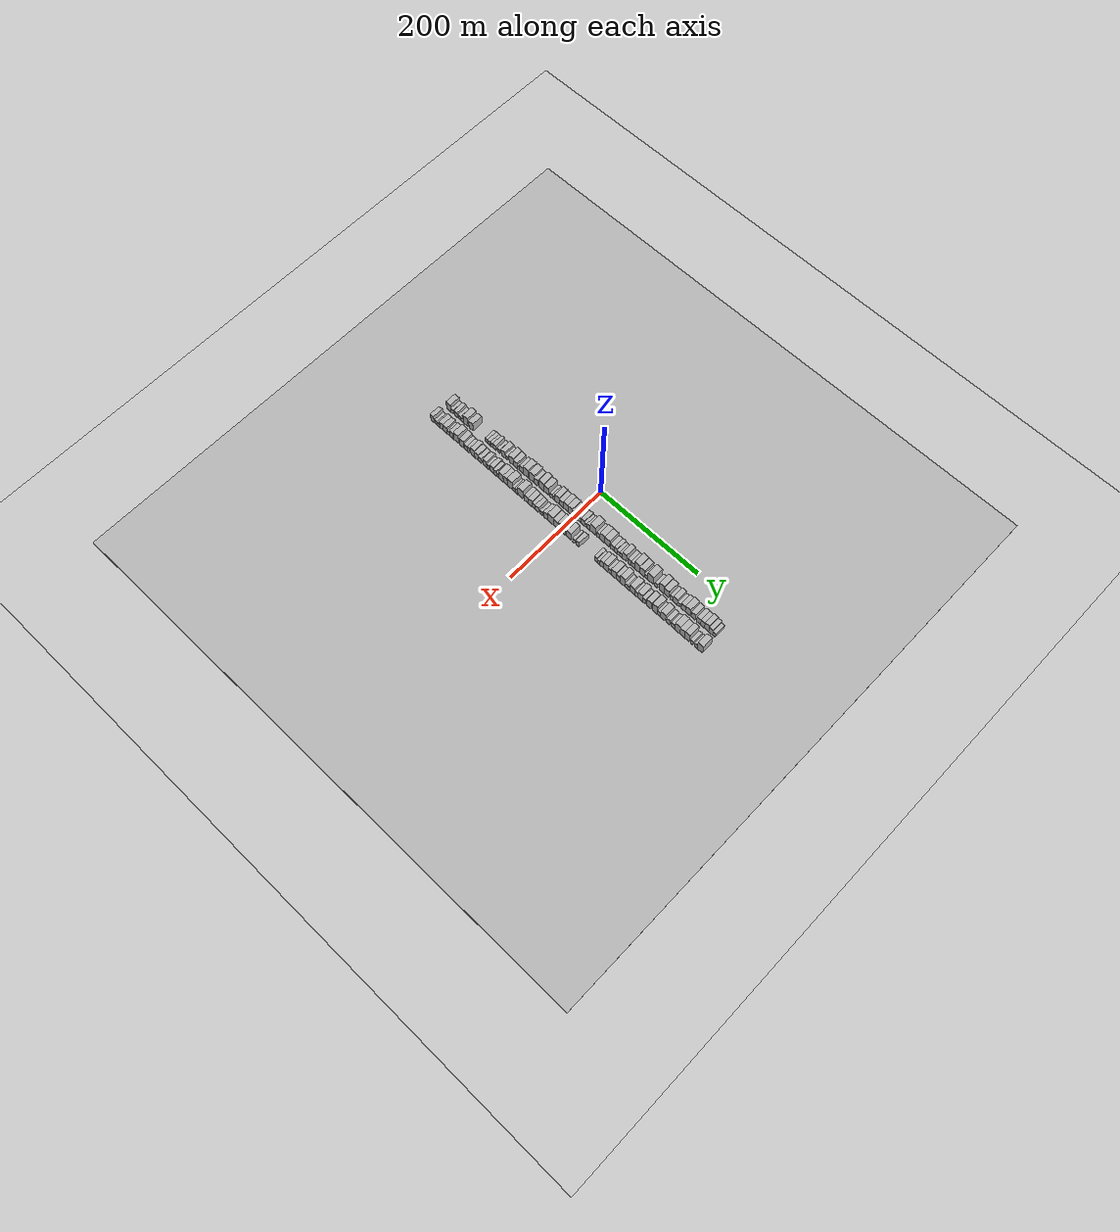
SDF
<?xml version="1.0" encoding="utf-8"?>

<sdf version="1.6">

   <world name="default">

      <gui fullscreen="0">

         <camera name="user_camera">

            <pose>-15 0 4.57585 0 0 0</pose>

            <view_controller>orbit</view_controller>

         </camera>

      </gui>

      <scene>

         <sky>

           <clouds>

             <speed>12</speed>

           </clouds>

         </sky>

         <ambient>0.4 0.4 0.4 1</ambient>

         <background>0.7 0.7 0.7 1</background>

         <shadows>1</shadows>

      </scene>

      <gravity>0 0 -9.8066</gravity>

      <magnetic_field>6e-06 2.3e-05 -4.2e-05</magnetic_field>

      <physics default="0" name="default_physics" type="ode">

         <ode>

            <solver>

               <type>quick</type>

               <iters>10</iters>

               <sor>1.0</sor>

               <use_dynamic_moi_rescaling>0</use_dynamic_moi_rescaling>

            </solver>

            <constraints>

               <cfm>0</cfm>

               <erp>0.2</erp>

               <contact_max_correcting_vel>100</contact_max_correcting_vel>

               <contact_surface_layer>0.001</contact_surface_layer>

            </constraints>

         </ode>

         <max_step_size>0.004</max_step_size>

         <real_time_factor>1</real_time_factor>

         <real_time_update_rate>250</real_time_update_rate>

      </physics>

      <light name="sun" type="directional">

         <cast_shadows>1</cast_shadows>

         <pose>0 0 10 0 0 0</pose>

         <diffuse>0.8 0.8 0.8 1</diffuse>

         <specular>0.2 0.2 0.2 1</specular>

         <attenuation>

            <range>1000</range>

            <constant>0.9</constant>

            <linear>0.01</linear>

            <quadratic>0.001</quadratic>

         </attenuation>

         <direction>-0.5 0.1 -0.9</direction>

      </light>

      <include>

         <name>ground_plane_1</name>

         <uri>model://HANNAS_ground_plane</uri>

         <pose>0 0 0  0 0 0</pose>

      </include>

      <include>

         <name>ground_plane_2</name>

         <uri>model://HANNAS_ground_plane</uri>

         <pose>100 0 0  0 0 0</pose>

      </include>

      <model name="building_1">

         <static>1</static>

         <pose frame="">50.0000 -276.0207 0 0.000000 0.000000 0.000000</pose>

         <link name="link">

            <pose frame="">0 0 10.50 0 0 0</pose>

            <collision name="collision">

               <geometry>

                  <box>

                     <size>20.0000 9.9586 21.0000</size>

                  </box>

               </geometry>

               <max_contacts>10</max_contacts>

               <surface>

                  <contact>

                     <ode/>

                  </contact>

                  <bounce/>

                  <friction>

                     <torsional>

                        <ode/>

                     </torsional>

                     <ode/>

                  </friction>

               </surface>

            </collision>

            <visual name="visual">

               <cast_shadows>0</cast_shadows>

               <geometry>

                  <box>

                     <size>20.0000 9.9586 21.0000</size>

                  </box>

               </geometry>

               <material>

                  <script>

                     <uri>model://HANNAS_wall/materials/scripts</uri>

                     <uri>model://HANNAS_wall/materials/textures</uri>

                     <name>vrc/HANNAS_wall</name>

                  </script>

               </material>

            </visual>

            <self_collide>0</self_collide>

            <enable_wind>0</enable_wind>

            <kinematic>0</kinematic>

         </link>

      </model>

      <model name="building_2">

         <static>1</static>

         <pose frame="">50.0000 -268.1680 0 0.000000 0.000000 0.000000</pose>

         <link name="link">

            <pose frame="">0 0 6.00 0 0 0</pose>

            <collision name="collision">

               <geometry>

                  <box>

                     <size>20.0000 5.7468 12.0000</size>

                  </box>

               </geometry>

               <max_contacts>10</max_contacts>

               <surface>

                  <contact>

                     <ode/>

                  </contact>

                  <bounce/>

                  <friction>

                     <torsional>

                        <ode/>

                     </torsional>

                     <ode/>

                  </friction>

               </surface>

            </collision>

            <visual name="visual">

               <cast_shadows>0</cast_shadows>

               <geometry>

                  <box>

                     <size>20.0000 5.7468 12.0000</size>

                  </box>

               </geometry>

               <material>

                  <script>

                     <uri>model://HANNAS_wall/materials/scripts</uri>

                     <uri>model://HANNAS_wall/materials/textures</uri>

                     <name>vrc/HANNAS_wall</name>

                  </script>

               </material>

            </visual>

            <self_collide>0</self_collide>

            <enable_wind>0</enable_wind>

            <kinematic>0</kinematic>

         </link>

      </model>

      <model name="building_3">

         <static>1</static>

         <pose frame="">50.0000 -259.8108 0 0.000000 0.000000 0.000000</pose>

         <link name="link">

            <pose frame="">0 0 7.50 0 0 0</pose>

            <collision name="collision">

               <geometry>

                  <box>

                     <size>20.0000 6.9677 15.0000</size>

                  </box>

               </geometry>

               <max_contacts>10</max_contacts>

               <surface>

                  <contact>

                     <ode/>

                  </contact>

                  <bounce/>

                  <friction>

                     <torsional>

                        <ode/>

                     </torsional>

                     <ode/>

                  </friction>

               </surface>

            </collision>

            <visual name="visual">

               <cast_shadows>0</cast_shadows>

               <geometry>

                  <box>

                     <size>20.0000 6.9677 15.0000</size>

                  </box>

               </geometry>

               <material>

                  <script>

                     <uri>model://HANNAS_wall/materials/scripts</uri>

                     <uri>model://HANNAS_wall/materials/textures</uri>

                     <name>vrc/HANNAS_wall</name>

                  </script>

               </material>

            </visual>

            <self_collide>0</self_collide>

            <enable_wind>0</enable_wind>

            <kinematic>0</kinematic>

         </link>

      </model>

      <model name="building_4">

         <static>1</static>

         <pose frame="">50.0000 -251.4593 0 0.000000 0.000000 0.000000</pose>

         <link name="link">

            <pose frame="">0 0 6.00 0 0 0</pose>

            <collision name="collision">

               <geometry>

                  <box>

                     <size>20.0000 5.7353 12.0000</size>

                  </box>

               </geometry>

               <max_contacts>10</max_contacts>

               <surface>

                  <contact>

                     <ode/>

                  </contact>

                  <bounce/>

                  <friction>

                     <torsional>

                        <ode/>

                     </torsional>

                     <ode/>

                  </friction>

               </surface>

            </collision>

            <visual name="visual">

               <cast_shadows>0</cast_shadows>

               <geometry>

                  <box>

                     <size>20.0000 5.7353 12.0000</size>

                  </box>

               </geometry>

               <material>

                  <script>

                     <uri>model://HANNAS_wall/materials/scripts</uri>

                     <uri>model://HANNAS_wall/materials/textures</uri>

                     <name>vrc/HANNAS_wall</name>

                  </script>

               </material>

            </visual>

            <self_collide>0</self_collide>

            <enable_wind>0</enable_wind>

            <kinematic>0</kinematic>

         </link>

      </model>

      <model name="building_5">

         <static>1</static>

         <pose frame="">50.0000 -245.6844 0 0.000000 0.000000 0.000000</pose>

         <link name="link">

            <pose frame="">0 0 6.00 0 0 0</pose>

            <collision name="collision">

               <geometry>

                  <box>

                     <size>20.0000 5.8143 12.0000</size>

                  </box>

               </geometry>

               <max_contacts>10</max_contacts>

               <surface>

                  <contact>

                     <ode/>

                  </contact>

                  <bounce/>

                  <friction>

                     <torsional>

                        <ode/>

                     </torsional>

                     <ode/>

                  </friction>

               </surface>

            </collision>

            <visual name="visual">

               <cast_shadows>0</cast_shadows>

               <geometry>

                  <box>

                     <size>20.0000 5.8143 12.0000</size>

                  </box>

               </geometry>

               <material>

                  <script>

                     <uri>model://HANNAS_wall/materials/scripts</uri>

                     <uri>model://HANNAS_wall/materials/textures</uri>

                     <name>vrc/HANNAS_wall</name>

                  </script>

               </material>

            </visual>

            <self_collide>0</self_collide>

            <enable_wind>0</enable_wind>

            <kinematic>0</kinematic>

         </link>

      </model>

      <model name="building_6">

         <static>1</static>

         <pose frame="">50.0000 -237.5638 0 0.000000 0.000000 0.000000</pose>

         <link name="link">

            <pose frame="">0 0 12.00 0 0 0</pose>

            <collision name="collision">

               <geometry>

                  <box>

                     <size>20.0000 10.4269 24.0000</size>

                  </box>

               </geometry>

               <max_contacts>10</max_contacts>

               <surface>

                  <contact>

                     <ode/>

                  </contact>

                  <bounce/>

                  <friction>

                     <torsional>

                        <ode/>

                     </torsional>

                     <ode/>

                  </friction>

               </surface>

            </collision>

            <visual name="visual">

               <cast_shadows>0</cast_shadows>

               <geometry>

                  <box>

                     <size>20.0000 10.4269 24.0000</size>

                  </box>

               </geometry>

               <material>

                  <script>

                     <uri>model://HANNAS_wall/materials/scripts</uri>

                     <uri>model://HANNAS_wall/materials/textures</uri>

                     <name>vrc/HANNAS_wall</name>

                  </script>

               </material>

            </visual>

            <self_collide>0</self_collide>

            <enable_wind>0</enable_wind>

            <kinematic>0</kinematic>

         </link>

      </model>

      <model name="building_7">

         <static>1</static>

         <pose frame="">50.0000 -225.5787 0 0.000000 0.000000 0.000000</pose>

         <link name="link">

            <pose frame="">0 0 10.50 0 0 0</pose>

            <collision name="collision">

               <geometry>

                  <box>

                     <size>20.0000 9.5435 21.0000</size>

                  </box>

               </geometry>

               <max_contacts>10</max_contacts>

               <surface>

                  <contact>

                     <ode/>

                  </contact>

                  <bounce/>

                  <friction>

                     <torsional>

                        <ode/>

                     </torsional>

                     <ode/>

                  </friction>

               </surface>

            </collision>

            <visual name="visual">

               <cast_shadows>0</cast_shadows>

               <geometry>

                  <box>

                     <size>20.0000 9.5435 21.0000</size>

                  </box>

               </geometry>

               <material>

                  <script>

                     <uri>model://HANNAS_wall/materials/scripts</uri>

                     <uri>model://HANNAS_wall/materials/textures</uri>

                     <name>vrc/HANNAS_wall</name>

                  </script>

               </material>

            </visual>

            <self_collide>0</self_collide>

            <enable_wind>0</enable_wind>

            <kinematic>0</kinematic>

         </link>

      </model>

      <model name="building_8">

         <static>1</static>

         <pose frame="">50.0000 -190.9284 0 0.000000 0.000000 0.000000</pose>

         <link name="link">

            <pose frame="">0 0 6.00 0 0 0</pose>

            <collision name="collision">

               <geometry>

                  <box>

                     <size>20.0000 5.2524 12.0000</size>

                  </box>

               </geometry>

               <max_contacts>10</max_contacts>

               <surface>

                  <contact>

                     <ode/>

                  </contact>

                  <bounce/>

                  <friction>

                     <torsional>

                        <ode/>

                     </torsional>

                     <ode/>

                  </friction>

               </surface>

            </collision>

            <visual name="visual">

               <cast_shadows>0</cast_shadows>

               <geometry>

                  <box>

                     <size>20.0000 5.2524 12.0000</size>

                  </box>

               </geometry>

               <material>

                  <script>

                     <uri>model://HANNAS_wall/materials/scripts</uri>

                     <uri>model://HANNAS_wall/materials/textures</uri>

                     <name>vrc/HANNAS_wall</name>

                  </script>

               </material>

            </visual>

            <self_collide>0</self_collide>

            <enable_wind>0</enable_wind>

            <kinematic>0</kinematic>

         </link>

      </model>

      <model name="building_9">

         <static>1</static>

         <pose frame="">50.0000 -185.3415 0 0.000000 0.000000 0.000000</pose>

         <link name="link">

            <pose frame="">0 0 6.00 0 0 0</pose>

            <collision name="collision">

               <geometry>

                  <box>

                     <size>20.0000 5.9213 12.0000</size>

                  </box>

               </geometry>

               <max_contacts>10</max_contacts>

               <surface>

                  <contact>

                     <ode/>

                  </contact>

                  <bounce/>

                  <friction>

                     <torsional>

                        <ode/>

                     </torsional>

                     <ode/>

                  </friction>

               </surface>

            </collision>

            <visual name="visual">

               <cast_shadows>0</cast_shadows>

               <geometry>

                  <box>

                     <size>20.0000 5.9213 12.0000</size>

                  </box>

               </geometry>

               <material>

                  <script>

                     <uri>model://HANNAS_wall/materials/scripts</uri>

                     <uri>model://HANNAS_wall/materials/textures</uri>

                     <name>vrc/HANNAS_wall</name>

                  </script>

               </material>

            </visual>

            <self_collide>0</self_collide>

            <enable_wind>0</enable_wind>

            <kinematic>0</kinematic>

         </link>

      </model>

      <model name="building_10">

         <static>1</static>

         <pose frame="">50.0000 -179.4432 0 0.000000 0.000000 0.000000</pose>

         <link name="link">

            <pose frame="">0 0 6.00 0 0 0</pose>

            <collision name="collision">

               <geometry>

                  <box>

                     <size>20.0000 5.8752 12.0000</size>

                  </box>

               </geometry>

               <max_contacts>10</max_contacts>

               <surface>

                  <contact>

                     <ode/>

                  </contact>

                  <bounce/>

                  <friction>

                     <torsional>

                        <ode/>

                     </torsional>

                     <ode/>

                  </friction>

               </surface>

            </collision>

            <visual name="visual">

               <cast_shadows>0</cast_shadows>

               <geometry>

                  <box>

                     <size>20.0000 5.8752 12.0000</size>

                  </box>

               </geometry>

               <material>

                  <script>

                     <uri>model://HANNAS_wall/materials/scripts</uri>

                     <uri>model://HANNAS_wall/materials/textures</uri>

                     <name>vrc/HANNAS_wall</name>

                  </script>

               </material>

            </visual>

            <self_collide>0</self_collide>

            <enable_wind>0</enable_wind>

            <kinematic>0</kinematic>

         </link>

      </model>

      <model name="building_11">

         <static>1</static>

         <pose frame="">50.0000 -173.2333 0 0.000000 0.000000 0.000000</pose>

         <link name="link">

            <pose frame="">0 0 7.50 0 0 0</pose>

            <collision name="collision">

               <geometry>

                  <box>

                     <size>20.0000 6.5448 15.0000</size>

                  </box>

               </geometry>

               <max_contacts>10</max_contacts>

               <surface>

                  <contact>

                     <ode/>

                  </contact>

                  <bounce/>

                  <friction>

                     <torsional>

                        <ode/>

                     </torsional>

                     <ode/>

                  </friction>

               </surface>

            </collision>

            <visual name="visual">

               <cast_shadows>0</cast_shadows>

               <geometry>

                  <box>

                     <size>20.0000 6.5448 15.0000</size>

                  </box>

               </geometry>

               <material>

                  <script>

                     <uri>model://HANNAS_wall/materials/scripts</uri>

                     <uri>model://HANNAS_wall/materials/textures</uri>

                     <name>vrc/HANNAS_wall</name>

                  </script>

               </material>

            </visual>

            <self_collide>0</self_collide>

            <enable_wind>0</enable_wind>

            <kinematic>0</kinematic>

         </link>

      </model>

      <model name="building_12">

         <static>1</static>

         <pose frame="">50.0000 -164.2267 0 0.000000 0.000000 0.000000</pose>

         <link name="link">

            <pose frame="">0 0 6.00 0 0 0</pose>

            <collision name="collision">

               <geometry>

                  <box>

                     <size>20.0000 5.4684 12.0000</size>

                  </box>

               </geometry>

               <max_contacts>10</max_contacts>

               <surface>

                  <contact>

                     <ode/>

                  </contact>

                  <bounce/>

                  <friction>

                     <torsional>

                        <ode/>

                     </torsional>

                     <ode/>

                  </friction>

               </surface>

            </collision>

            <visual name="visual">

               <cast_shadows>0</cast_shadows>

               <geometry>

                  <box>

                     <size>20.0000 5.4684 12.0000</size>

                  </box>

               </geometry>

               <material>

                  <script>

                     <uri>model://HANNAS_wall/materials/scripts</uri>

                     <uri>model://HANNAS_wall/materials/textures</uri>

                     <name>vrc/HANNAS_wall</name>

                  </script>

               </material>

            </visual>

            <self_collide>0</self_collide>

            <enable_wind>0</enable_wind>

            <kinematic>0</kinematic>

         </link>

      </model>

      <model name="building_13">

         <static>1</static>

         <pose frame="">50.0000 -154.0466 0 0.000000 0.000000 0.000000</pose>

         <link name="link">

            <pose frame="">0 0 9.00 0 0 0</pose>

            <collision name="collision">

               <geometry>

                  <box>

                     <size>20.0000 8.8918 18.0000</size>

                  </box>

               </geometry>

               <max_contacts>10</max_contacts>

               <surface>

                  <contact>

                     <ode/>

                  </contact>

                  <bounce/>

                  <friction>

                     <torsional>

                        <ode/>

                     </torsional>

                     <ode/>

                  </friction>

               </surface>

            </collision>

            <visual name="visual">

               <cast_shadows>0</cast_shadows>

               <geometry>

                  <box>

                     <size>20.0000 8.8918 18.0000</size>

                  </box>

               </geometry>

               <material>

                  <script>

                     <uri>model://HANNAS_wall/materials/scripts</uri>

                     <uri>model://HANNAS_wall/materials/textures</uri>

                     <name>vrc/HANNAS_wall</name>

                  </script>

               </material>

            </visual>

            <self_collide>0</self_collide>

            <enable_wind>0</enable_wind>

            <kinematic>0</kinematic>

         </link>

      </model>

      <model name="building_14">

         <static>1</static>

         <pose frame="">50.0000 -146.9675 0 0.000000 0.000000 0.000000</pose>

         <link name="link">

            <pose frame="">0 0 6.00 0 0 0</pose>

            <collision name="collision">

               <geometry>

                  <box>

                     <size>20.0000 5.2665 12.0000</size>

                  </box>

               </geometry>

               <max_contacts>10</max_contacts>

               <surface>

                  <contact>

                     <ode/>

                  </contact>

                  <bounce/>

                  <friction>

                     <torsional>

                        <ode/>

                     </torsional>

                     <ode/>

                  </friction>

               </surface>

            </collision>

            <visual name="visual">

               <cast_shadows>0</cast_shadows>

               <geometry>

                  <box>

                     <size>20.0000 5.2665 12.0000</size>

                  </box>

               </geometry>

               <material>

                  <script>

                     <uri>model://HANNAS_wall/materials/scripts</uri>

                     <uri>model://HANNAS_wall/materials/textures</uri>

                     <name>vrc/HANNAS_wall</name>

                  </script>

               </material>

            </visual>

            <self_collide>0</self_collide>

            <enable_wind>0</enable_wind>

            <kinematic>0</kinematic>

         </link>

      </model>

      <model name="building_15">

         <static>1</static>

         <pose frame="">50.0000 -136.4984 0 0.000000 0.000000 0.000000</pose>

         <link name="link">

            <pose frame="">0 0 10.50 0 0 0</pose>

            <collision name="collision">

               <geometry>

                  <box>

                     <size>20.0000 9.6715 21.0000</size>

                  </box>

               </geometry>

               <max_contacts>10</max_contacts>

               <surface>

                  <contact>

                     <ode/>

                  </contact>

                  <bounce/>

                  <friction>

                     <torsional>

                        <ode/>

                     </torsional>

                     <ode/>

                  </friction>

               </surface>

            </collision>

            <visual name="visual">

               <cast_shadows>0</cast_shadows>

               <geometry>

                  <box>

                     <size>20.0000 9.6715 21.0000</size>

                  </box>

               </geometry>

               <material>

                  <script>

                     <uri>model://HANNAS_wall/materials/scripts</uri>

                     <uri>model://HANNAS_wall/materials/textures</uri>

                     <name>vrc/HANNAS_wall</name>

                  </script>

               </material>

            </visual>

            <self_collide>0</self_collide>

            <enable_wind>0</enable_wind>

            <kinematic>0</kinematic>

         </link>

      </model>

      <model name="building_16">

         <static>1</static>

         <pose frame="">50.0000 -127.2454 0 0.000000 0.000000 0.000000</pose>

         <link name="link">

            <pose frame="">0 0 9.00 0 0 0</pose>

            <collision name="collision">

               <geometry>

                  <box>

                     <size>20.0000 8.8345 18.0000</size>

                  </box>

               </geometry>

               <max_contacts>10</max_contacts>

               <surface>

                  <contact>

                     <ode/>

                  </contact>

                  <bounce/>

                  <friction>

                     <torsional>

                        <ode/>

                     </torsional>

                     <ode/>

                  </friction>

               </surface>

            </collision>

            <visual name="visual">

               <cast_shadows>0</cast_shadows>

               <geometry>

                  <box>

                     <size>20.0000 8.8345 18.0000</size>

                  </box>

               </geometry>

               <material>

                  <script>

                     <uri>model://HANNAS_wall/materials/scripts</uri>

                     <uri>model://HANNAS_wall/materials/textures</uri>

                     <name>vrc/HANNAS_wall</name>

                  </script>

               </material>

            </visual>

            <self_collide>0</self_collide>

            <enable_wind>0</enable_wind>

            <kinematic>0</kinematic>

         </link>

      </model>

      <model name="building_17">

         <static>1</static>

         <pose frame="">50.0000 -120.4018 0 0.000000 0.000000 0.000000</pose>

         <link name="link">

            <pose frame="">0 0 6.00 0 0 0</pose>

            <collision name="collision">

               <geometry>

                  <box>

                     <size>20.0000 4.8527 12.0000</size>

                  </box>

               </geometry>

               <max_contacts>10</max_contacts>

               <surface>

                  <contact>

                     <ode/>

                  </contact>

                  <bounce/>

                  <friction>

                     <torsional>

                        <ode/>

                     </torsional>

                     <ode/>

                  </friction>

               </surface>

            </collision>

            <visual name="visual">

               <cast_shadows>0</cast_shadows>

               <geometry>

                  <box>

                     <size>20.0000 4.8527 12.0000</size>

                  </box>

               </geometry>

               <material>

                  <script>

                     <uri>model://HANNAS_wall/materials/scripts</uri>

                     <uri>model://HANNAS_wall/materials/textures</uri>

                     <name>vrc/HANNAS_wall</name>

                  </script>

               </material>

            </visual>

            <self_collide>0</self_collide>

            <enable_wind>0</enable_wind>

            <kinematic>0</kinematic>

         </link>

      </model>

      <model name="building_18">

         <static>1</static>

         <pose frame="">50.0000 -113.9878 0 0.000000 0.000000 0.000000</pose>

         <link name="link">

            <pose frame="">0 0 9.00 0 0 0</pose>

            <collision name="collision">

               <geometry>

                  <box>

                     <size>20.0000 7.9753 18.0000</size>

                  </box>

               </geometry>

               <max_contacts>10</max_contacts>

               <surface>

                  <contact>

                     <ode/>

                  </contact>

                  <bounce/>

                  <friction>

                     <torsional>

                        <ode/>

                     </torsional>

                     <ode/>

                  </friction>

               </surface>

            </collision>

            <visual name="visual">

               <cast_shadows>0</cast_shadows>

               <geometry>

                  <box>

                     <size>20.0000 7.9753 18.0000</size>

                  </box>

               </geometry>

               <material>

                  <script>

                     <uri>model://HANNAS_wall/materials/scripts</uri>

                     <uri>model://HANNAS_wall/materials/textures</uri>

                     <name>vrc/HANNAS_wall</name>

                  </script>

               </material>

            </visual>

            <self_collide>0</self_collide>

            <enable_wind>0</enable_wind>

            <kinematic>0</kinematic>

         </link>

      </model>

      <model name="building_19">

         <static>1</static>

         <pose frame="">50.0000 -104.5113 0 0.000000 0.000000 0.000000</pose>

         <link name="link">

            <pose frame="">0 0 12.00 0 0 0</pose>

            <collision name="collision">

               <geometry>

                  <box>

                     <size>20.0000 10.9776 24.0000</size>

                  </box>

               </geometry>

               <max_contacts>10</max_contacts>

               <surface>

                  <contact>

                     <ode/>

                  </contact>

                  <bounce/>

                  <friction>

                     <torsional>

                        <ode/>

                     </torsional>

                     <ode/>

                  </friction>

               </surface>

            </collision>

            <visual name="visual">

               <cast_shadows>0</cast_shadows>

               <geometry>

                  <box>

                     <size>20.0000 10.9776 24.0000</size>

                  </box>

               </geometry>

               <material>

                  <script>

                     <uri>model://HANNAS_wall/materials/scripts</uri>

                     <uri>model://HANNAS_wall/materials/textures</uri>

                     <name>vrc/HANNAS_wall</name>

                  </script>

               </material>

            </visual>

            <self_collide>0</self_collide>

            <enable_wind>0</enable_wind>

            <kinematic>0</kinematic>

         </link>

      </model>

      <model name="building_20">

         <static>1</static>

         <pose frame="">50.0000 -91.5438 0 0.000000 0.000000 0.000000</pose>

         <link name="link">

            <pose frame="">0 0 12.00 0 0 0</pose>

            <collision name="collision">

               <geometry>

                  <box>

                     <size>20.0000 10.9575 24.0000</size>

                  </box>

               </geometry>

               <max_contacts>10</max_contacts>

               <surface>

                  <contact>

                     <ode/>

                  </contact>

                  <bounce/>

                  <friction>

                     <torsional>

                        <ode/>

                     </torsional>

                     <ode/>

                  </friction>

               </surface>

            </collision>

            <visual name="visual">

               <cast_shadows>0</cast_shadows>

               <geometry>

                  <box>

                     <size>20.0000 10.9575 24.0000</size>

                  </box>

               </geometry>

               <material>

                  <script>

                     <uri>model://HANNAS_wall/materials/scripts</uri>

                     <uri>model://HANNAS_wall/materials/textures</uri>

                     <name>vrc/HANNAS_wall</name>

                  </script>

               </material>

            </visual>

            <self_collide>0</self_collide>

            <enable_wind>0</enable_wind>

            <kinematic>0</kinematic>

         </link>

      </model>

      <model name="building_21">

         <static>1</static>

         <pose frame="">50.0000 -82.3586 0 0.000000 0.000000 0.000000</pose>

         <link name="link">

            <pose frame="">0 0 9.00 0 0 0</pose>

            <collision name="collision">

               <geometry>

                  <box>

                     <size>20.0000 7.4127 18.0000</size>

                  </box>

               </geometry>

               <max_contacts>10</max_contacts>

               <surface>

                  <contact>

                     <ode/>

                  </contact>

                  <bounce/>

                  <friction>

                     <torsional>

                        <ode/>

                     </torsional>

                     <ode/>

                  </friction>

               </surface>

            </collision>

            <visual name="visual">

               <cast_shadows>0</cast_shadows>

               <geometry>

                  <box>

                     <size>20.0000 7.4127 18.0000</size>

                  </box>

               </geometry>

               <material>

                  <script>

                     <uri>model://HANNAS_wall/materials/scripts</uri>

                     <uri>model://HANNAS_wall/materials/textures</uri>

                     <name>vrc/HANNAS_wall</name>

                  </script>

               </material>

            </visual>

            <self_collide>0</self_collide>

            <enable_wind>0</enable_wind>

            <kinematic>0</kinematic>

         </link>

      </model>

      <model name="building_22">

         <static>1</static>

         <pose frame="">50.0000 -70.5201 0 0.000000 0.000000 0.000000</pose>

         <link name="link">

            <pose frame="">0 0 12.00 0 0 0</pose>

            <collision name="collision">

               <geometry>

                  <box>

                     <size>20.0000 10.2644 24.0000</size>

                  </box>

               </geometry>

               <max_contacts>10</max_contacts>

               <surface>

                  <contact>

                     <ode/>

                  </contact>

                  <bounce/>

                  <friction>

                     <torsional>

                        <ode/>

                     </torsional>

                     <ode/>

                  </friction>

               </surface>

            </collision>

            <visual name="visual">

               <cast_shadows>0</cast_shadows>

               <geometry>

                  <box>

                     <size>20.0000 10.2644 24.0000</size>

                  </box>

               </geometry>

               <material>

                  <script>

                     <uri>model://HANNAS_wall/materials/scripts</uri>

                     <uri>model://HANNAS_wall/materials/textures</uri>

                     <name>vrc/HANNAS_wall</name>

                  </script>

               </material>

            </visual>

            <self_collide>0</self_collide>

            <enable_wind>0</enable_wind>

            <kinematic>0</kinematic>

         </link>

      </model>

      <model name="building_23">

         <static>1</static>

         <pose frame="">50.0000 -60.4606 0 0.000000 0.000000 0.000000</pose>

         <link name="link">

            <pose frame="">0 0 10.50 0 0 0</pose>

            <collision name="collision">

               <geometry>

                  <box>

                     <size>20.0000 9.8546 21.0000</size>

                  </box>

               </geometry>

               <max_contacts>10</max_contacts>

               <surface>

                  <contact>

                     <ode/>

                  </contact>

                  <bounce/>

                  <friction>

                     <torsional>

                        <ode/>

                     </torsional>

                     <ode/>

                  </friction>

               </surface>

            </collision>

            <visual name="visual">

               <cast_shadows>0</cast_shadows>

               <geometry>

                  <box>

                     <size>20.0000 9.8546 21.0000</size>

                  </box>

               </geometry>

               <material>

                  <script>

                     <uri>model://HANNAS_wall/materials/scripts</uri>

                     <uri>model://HANNAS_wall/materials/textures</uri>

                     <name>vrc/HANNAS_wall</name>

                  </script>

               </material>

            </visual>

            <self_collide>0</self_collide>

            <enable_wind>0</enable_wind>

            <kinematic>0</kinematic>

         </link>

      </model>

      <model name="building_24">

         <static>1</static>

         <pose frame="">50.0000 -50.1069 0 0.000000 0.000000 0.000000</pose>

         <link name="link">

            <pose frame="">0 0 6.00 0 0 0</pose>

            <collision name="collision">

               <geometry>

                  <box>

                     <size>20.0000 4.8529 12.0000</size>

                  </box>

               </geometry>

               <max_contacts>10</max_contacts>

               <surface>

                  <contact>

                     <ode/>

                  </contact>

                  <bounce/>

                  <friction>

                     <torsional>

                        <ode/>

                     </torsional>

                     <ode/>

                  </friction>

               </surface>

            </collision>

            <visual name="visual">

               <cast_shadows>0</cast_shadows>

               <geometry>

                  <box>

                     <size>20.0000 4.8529 12.0000</size>

                  </box>

               </geometry>

               <material>

                  <script>

                     <uri>model://HANNAS_wall/materials/scripts</uri>

                     <uri>model://HANNAS_wall/materials/textures</uri>

                     <name>vrc/HANNAS_wall</name>

                  </script>

               </material>

            </visual>

            <self_collide>0</self_collide>

            <enable_wind>0</enable_wind>

            <kinematic>0</kinematic>

         </link>

      </model>

      <model name="building_25">

         <static>1</static>

         <pose frame="">50.0000 -44.7329 0 0.000000 0.000000 0.000000</pose>

         <link name="link">

            <pose frame="">0 0 6.00 0 0 0</pose>

            <collision name="collision">

               <geometry>

                  <box>

                     <size>20.0000 5.8950 12.0000</size>

                  </box>

               </geometry>

               <max_contacts>10</max_contacts>

               <surface>

                  <contact>

                     <ode/>

                  </contact>

                  <bounce/>

                  <friction>

                     <torsional>

                        <ode/>

                     </torsional>

                     <ode/>

                  </friction>

               </surface>

            </collision>

            <visual name="visual">

               <cast_shadows>0</cast_shadows>

               <geometry>

                  <box>

                     <size>20.0000 5.8950 12.0000</size>

                  </box>

               </geometry>

               <material>

                  <script>

                     <uri>model://HANNAS_wall/materials/scripts</uri>

                     <uri>model://HANNAS_wall/materials/textures</uri>

                     <name>vrc/HANNAS_wall</name>

                  </script>

               </material>

            </visual>

            <self_collide>0</self_collide>

            <enable_wind>0</enable_wind>

            <kinematic>0</kinematic>

         </link>

      </model>

      <model name="building_26">

         <static>1</static>

         <pose frame="">50.0000 -37.0605 0 0.000000 0.000000 0.000000</pose>

         <link name="link">

            <pose frame="">0 0 10.50 0 0 0</pose>

            <collision name="collision">

               <geometry>

                  <box>

                     <size>20.0000 9.4498 21.0000</size>

                  </box>

               </geometry>

               <max_contacts>10</max_contacts>

               <surface>

                  <contact>

                     <ode/>

                  </contact>

                  <bounce/>

                  <friction>

                     <torsional>

                        <ode/>

                     </torsional>

                     <ode/>

                  </friction>

               </surface>

            </collision>

            <visual name="visual">

               <cast_shadows>0</cast_shadows>

               <geometry>

                  <box>

                     <size>20.0000 9.4498 21.0000</size>

                  </box>

               </geometry>

               <material>

                  <script>

                     <uri>model://HANNAS_wall/materials/scripts</uri>

                     <uri>model://HANNAS_wall/materials/textures</uri>

                     <name>vrc/HANNAS_wall</name>

                  </script>

               </material>

            </visual>

            <self_collide>0</self_collide>

            <enable_wind>0</enable_wind>

            <kinematic>0</kinematic>

         </link>

      </model>

      <model name="building_27">

         <static>1</static>

         <pose frame="">50.0000 -27.8437 0 0.000000 0.000000 0.000000</pose>

         <link name="link">

            <pose frame="">0 0 9.00 0 0 0</pose>

            <collision name="collision">

               <geometry>

                  <box>

                     <size>20.0000 8.9838 18.0000</size>

                  </box>

               </geometry>

               <max_contacts>10</max_contacts>

               <surface>

                  <contact>

                     <ode/>

                  </contact>

                  <bounce/>

                  <friction>

                     <torsional>

                        <ode/>

                     </torsional>

                     <ode/>

                  </friction>

               </surface>

            </collision>

            <visual name="visual">

               <cast_shadows>0</cast_shadows>

               <geometry>

                  <box>

                     <size>20.0000 8.9838 18.0000</size>

                  </box>

               </geometry>

               <material>

                  <script>

                     <uri>model://HANNAS_wall/materials/scripts</uri>

                     <uri>model://HANNAS_wall/materials/textures</uri>

                     <name>vrc/HANNAS_wall</name>

                  </script>

               </material>

            </visual>

            <self_collide>0</self_collide>

            <enable_wind>0</enable_wind>

            <kinematic>0</kinematic>

         </link>

      </model>

      <model name="building_28">

         <static>1</static>

         <pose frame="">50.0000 -18.8576 0 0.000000 0.000000 0.000000</pose>

         <link name="link">

            <pose frame="">0 0 10.50 0 0 0</pose>

            <collision name="collision">

               <geometry>

                  <box>

                     <size>20.0000 8.9882 21.0000</size>

                  </box>

               </geometry>

               <max_contacts>10</max_contacts>

               <surface>

                  <contact>

                     <ode/>

                  </contact>

                  <bounce/>

                  <friction>

                     <torsional>

                        <ode/>

                     </torsional>

                     <ode/>

                  </friction>

               </surface>

            </collision>

            <visual name="visual">

               <cast_shadows>0</cast_shadows>

               <geometry>

                  <box>

                     <size>20.0000 8.9882 21.0000</size>

                  </box>

               </geometry>

               <material>

                  <script>

                     <uri>model://HANNAS_wall/materials/scripts</uri>

                     <uri>model://HANNAS_wall/materials/textures</uri>

                     <name>vrc/HANNAS_wall</name>

                  </script>

               </material>

            </visual>

            <self_collide>0</self_collide>

            <enable_wind>0</enable_wind>

            <kinematic>0</kinematic>

         </link>

      </model>

      <model name="building_29">

         <static>1</static>

         <pose frame="">50.0000 -9.6039 0 0.000000 0.000000 0.000000</pose>

         <link name="link">

            <pose frame="">0 0 10.50 0 0 0</pose>

            <collision name="collision">

               <geometry>

                  <box>

                     <size>20.0000 9.5193 21.0000</size>

                  </box>

               </geometry>

               <max_contacts>10</max_contacts>

               <surface>

                  <contact>

                     <ode/>

                  </contact>

                  <bounce/>

                  <friction>

                     <torsional>

                        <ode/>

                     </torsional>

                     <ode/>

                  </friction>

               </surface>

            </collision>

            <visual name="visual">

               <cast_shadows>0</cast_shadows>

               <geometry>

                  <box>

                     <size>20.0000 9.5193 21.0000</size>

                  </box>

               </geometry>

               <material>

                  <script>

                     <uri>model://HANNAS_wall/materials/scripts</uri>

                     <uri>model://HANNAS_wall/materials/textures</uri>

                     <name>vrc/HANNAS_wall</name>

                  </script>

               </material>

            </visual>

            <self_collide>0</self_collide>

            <enable_wind>0</enable_wind>

            <kinematic>0</kinematic>

         </link>

      </model>

      <model name="building_30">

         <static>1</static>

         <pose frame="">50.0000 -0.8209 0 0.000000 0.000000 0.000000</pose>

         <link name="link">

            <pose frame="">0 0 9.00 0 0 0</pose>

            <collision name="collision">

               <geometry>

                  <box>

                     <size>20.0000 8.0467 18.0000</size>

                  </box>

               </geometry>

               <max_contacts>10</max_contacts>

               <surface>

                  <contact>

                     <ode/>

                  </contact>

                  <bounce/>

                  <friction>

                     <torsional>

                        <ode/>

                     </torsional>

                     <ode/>

                  </friction>

               </surface>

            </collision>

            <visual name="visual">

               <cast_shadows>0</cast_shadows>

               <geometry>

                  <box>

                     <size>20.0000 8.0467 18.0000</size>

                  </box>

               </geometry>

               <material>

                  <script>

                     <uri>model://HANNAS_wall/materials/scripts</uri>

                     <uri>model://HANNAS_wall/materials/textures</uri>

                     <name>vrc/HANNAS_wall</name>

                  </script>

               </material>

            </visual>

            <self_collide>0</self_collide>

            <enable_wind>0</enable_wind>

            <kinematic>0</kinematic>

         </link>

      </model>

      <model name="building_31">

         <static>1</static>

         <pose frame="">50.0000 9.9251 0 0.000000 0.000000 0.000000</pose>

         <link name="link">

            <pose frame="">0 0 7.50 0 0 0</pose>

            <collision name="collision">

               <geometry>

                  <box>

                     <size>20.0000 7.4453 15.0000</size>

                  </box>

               </geometry>

               <max_contacts>10</max_contacts>

               <surface>

                  <contact>

                     <ode/>

                  </contact>

                  <bounce/>

                  <friction>

                     <torsional>

                        <ode/>

                     </torsional>

                     <ode/>

                  </friction>

               </surface>

            </collision>

            <visual name="visual">

               <cast_shadows>0</cast_shadows>

               <geometry>

                  <box>

                     <size>20.0000 7.4453 15.0000</size>

                  </box>

               </geometry>

               <material>

                  <script>

                     <uri>model://HANNAS_wall/materials/scripts</uri>

                     <uri>model://HANNAS_wall/materials/textures</uri>

                     <name>vrc/HANNAS_wall</name>

                  </script>

               </material>

            </visual>

            <self_collide>0</self_collide>

            <enable_wind>0</enable_wind>

            <kinematic>0</kinematic>

         </link>

      </model>

      <model name="building_32">

         <static>1</static>

         <pose frame="">50.0000 17.2544 0 0.000000 0.000000 0.000000</pose>

         <link name="link">

            <pose frame="">0 0 7.50 0 0 0</pose>

            <collision name="collision">

               <geometry>

                  <box>

                     <size>20.0000 7.2133 15.0000</size>

                  </box>

               </geometry>

               <max_contacts>10</max_contacts>

               <surface>

                  <contact>

                     <ode/>

                  </contact>

                  <bounce/>

                  <friction>

                     <torsional>

                        <ode/>

                     </torsional>

                     <ode/>

                  </friction>

               </surface>

            </collision>

            <visual name="visual">

               <cast_shadows>0</cast_shadows>

               <geometry>

                  <box>

                     <size>20.0000 7.2133 15.0000</size>

                  </box>

               </geometry>

               <material>

                  <script>

                     <uri>model://HANNAS_wall/materials/scripts</uri>

                     <uri>model://HANNAS_wall/materials/textures</uri>

                     <name>vrc/HANNAS_wall</name>

                  </script>

               </material>

            </visual>

            <self_collide>0</self_collide>

            <enable_wind>0</enable_wind>

            <kinematic>0</kinematic>

         </link>

      </model>

      <model name="building_33">

         <static>1</static>

         <pose frame="">50.0000 23.6577 0 0.000000 0.000000 0.000000</pose>

         <link name="link">

            <pose frame="">0 0 6.00 0 0 0</pose>

            <collision name="collision">

               <geometry>

                  <box>

                     <size>20.0000 5.5933 12.0000</size>

                  </box>

               </geometry>

               <max_contacts>10</max_contacts>

               <surface>

                  <contact>

                     <ode/>

                  </contact>

                  <bounce/>

                  <friction>

                     <torsional>

                        <ode/>

                     </torsional>

                     <ode/>

                  </friction>

               </surface>

            </collision>

            <visual name="visual">

               <cast_shadows>0</cast_shadows>

               <geometry>

                  <box>

                     <size>20.0000 5.5933 12.0000</size>

                  </box>

               </geometry>

               <material>

                  <script>

                     <uri>model://HANNAS_wall/materials/scripts</uri>

                     <uri>model://HANNAS_wall/materials/textures</uri>

                     <name>vrc/HANNAS_wall</name>

                  </script>

               </material>

            </visual>

            <self_collide>0</self_collide>

            <enable_wind>0</enable_wind>

            <kinematic>0</kinematic>

         </link>

      </model>

      <model name="building_34">

         <static>1</static>

         <pose frame="">50.0000 29.6314 0 0.000000 0.000000 0.000000</pose>

         <link name="link">

            <pose frame="">0 0 7.50 0 0 0</pose>

            <collision name="collision">

               <geometry>

                  <box>

                     <size>20.0000 6.3542 15.0000</size>

                  </box>

               </geometry>

               <max_contacts>10</max_contacts>

               <surface>

                  <contact>

                     <ode/>

                  </contact>

                  <bounce/>

                  <friction>

                     <torsional>

                        <ode/>

                     </torsional>

                     <ode/>

                  </friction>

               </surface>

            </collision>

            <visual name="visual">

               <cast_shadows>0</cast_shadows>

               <geometry>

                  <box>

                     <size>20.0000 6.3542 15.0000</size>

                  </box>

               </geometry>

               <material>

                  <script>

                     <uri>model://HANNAS_wall/materials/scripts</uri>

                     <uri>model://HANNAS_wall/materials/textures</uri>

                     <name>vrc/HANNAS_wall</name>

                  </script>

               </material>

            </visual>

            <self_collide>0</self_collide>

            <enable_wind>0</enable_wind>

            <kinematic>0</kinematic>

         </link>

      </model>

      <model name="building_35">

         <static>1</static>

         <pose frame="">50.0000 38.7685 0 0.000000 0.000000 0.000000</pose>

         <link name="link">

            <pose frame="">0 0 12.00 0 0 0</pose>

            <collision name="collision">

               <geometry>

                  <box>

                     <size>20.0000 11.9199 24.0000</size>

                  </box>

               </geometry>

               <max_contacts>10</max_contacts>

               <surface>

                  <contact>

                     <ode/>

                  </contact>

                  <bounce/>

                  <friction>

                     <torsional>

                        <ode/>

                     </torsional>

                     <ode/>

                  </friction>

               </surface>

            </collision>

            <visual name="visual">

               <cast_shadows>0</cast_shadows>

               <geometry>

                  <box>

                     <size>20.0000 11.9199 24.0000</size>

                  </box>

               </geometry>

               <material>

                  <script>

                     <uri>model://HANNAS_wall/materials/scripts</uri>

                     <uri>model://HANNAS_wall/materials/textures</uri>

                     <name>vrc/HANNAS_wall</name>

                  </script>

               </material>

            </visual>

            <self_collide>0</self_collide>

            <enable_wind>0</enable_wind>

            <kinematic>0</kinematic>

         </link>

      </model>

      <model name="building_36">

         <static>1</static>

         <pose frame="">50.0000 50.0212 0 0.000000 0.000000 0.000000</pose>

         <link name="link">

            <pose frame="">0 0 7.50 0 0 0</pose>

            <collision name="collision">

               <geometry>

                  <box>

                     <size>20.0000 6.5854 15.0000</size>

                  </box>

               </geometry>

               <max_contacts>10</max_contacts>

               <surface>

                  <contact>

                     <ode/>

                  </contact>

                  <bounce/>

                  <friction>

                     <torsional>

                        <ode/>

                     </torsional>

                     <ode/>

                  </friction>

               </surface>

            </collision>

            <visual name="visual">

               <cast_shadows>0</cast_shadows>

               <geometry>

                  <box>

                     <size>20.0000 6.5854 15.0000</size>

                  </box>

               </geometry>

               <material>

                  <script>

                     <uri>model://HANNAS_wall/materials/scripts</uri>

                     <uri>model://HANNAS_wall/materials/textures</uri>

                     <name>vrc/HANNAS_wall</name>

                  </script>

               </material>

            </visual>

            <self_collide>0</self_collide>

            <enable_wind>0</enable_wind>

            <kinematic>0</kinematic>

         </link>

      </model>

      <model name="building_37">

         <static>1</static>

         <pose frame="">50.0000 58.3000 0 0.000000 0.000000 0.000000</pose>

         <link name="link">

            <pose frame="">0 0 10.50 0 0 0</pose>

            <collision name="collision">

               <geometry>

                  <box>

                     <size>20.0000 9.9722 21.0000</size>

                  </box>

               </geometry>

               <max_contacts>10</max_contacts>

               <surface>

                  <contact>

                     <ode/>

                  </contact>

                  <bounce/>

                  <friction>

                     <torsional>

                        <ode/>

                     </torsional>

                     <ode/>

                  </friction>

               </surface>

            </collision>

            <visual name="visual">

               <cast_shadows>0</cast_shadows>

               <geometry>

                  <box>

                     <size>20.0000 9.9722 21.0000</size>

                  </box>

               </geometry>

               <material>

                  <script>

                     <uri>model://HANNAS_wall/materials/scripts</uri>

                     <uri>model://HANNAS_wall/materials/textures</uri>

                     <name>vrc/HANNAS_wall</name>

                  </script>

               </material>

            </visual>

            <self_collide>0</self_collide>

            <enable_wind>0</enable_wind>

            <kinematic>0</kinematic>

         </link>

      </model>

      <model name="building_38">

         <static>1</static>

         <pose frame="">50.0000 68.4971 0 0.000000 0.000000 0.000000</pose>

         <link name="link">

            <pose frame="">0 0 10.50 0 0 0</pose>

            <collision name="collision">

               <geometry>

                  <box>

                     <size>20.0000 10.4220 21.0000</size>

                  </box>

               </geometry>

               <max_contacts>10</max_contacts>

               <surface>

                  <contact>

                     <ode/>

                  </contact>

                  <bounce/>

                  <friction>

                     <torsional>

                        <ode/>

                     </torsional>

                     <ode/>

                  </friction>

               </surface>

            </collision>

            <visual name="visual">

               <cast_shadows>0</cast_shadows>

               <geometry>

                  <box>

                     <size>20.0000 10.4220 21.0000</size>

                  </box>

               </geometry>

               <material>

                  <script>

                     <uri>model://HANNAS_wall/materials/scripts</uri>

                     <uri>model://HANNAS_wall/materials/textures</uri>

                     <name>vrc/HANNAS_wall</name>

                  </script>

               </material>

            </visual>

            <self_collide>0</self_collide>

            <enable_wind>0</enable_wind>

            <kinematic>0</kinematic>

         </link>

      </model>

      <model name="building_39">

         <static>1</static>

         <pose frame="">50.0000 79.3387 0 0.000000 0.000000 0.000000</pose>

         <link name="link">

            <pose frame="">0 0 7.50 0 0 0</pose>

            <collision name="collision">

               <geometry>

                  <box>

                     <size>20.0000 7.2612 15.0000</size>

                  </box>

               </geometry>

               <max_contacts>10</max_contacts>

               <surface>

                  <contact>

                     <ode/>

                  </contact>

                  <bounce/>

                  <friction>

                     <torsional>

                        <ode/>

                     </torsional>

                     <ode/>

                  </friction>

               </surface>

            </collision>

            <visual name="visual">

               <cast_shadows>0</cast_shadows>

               <geometry>

                  <box>

                     <size>20.0000 7.2612 15.0000</size>

                  </box>

               </geometry>

               <material>

                  <script>

                     <uri>model://HANNAS_wall/materials/scripts</uri>

                     <uri>model://HANNAS_wall/materials/textures</uri>

                     <name>vrc/HANNAS_wall</name>

                  </script>

               </material>

            </visual>

            <self_collide>0</self_collide>

            <enable_wind>0</enable_wind>

            <kinematic>0</kinematic>

         </link>

      </model>

      <model name="building_40">

         <static>1</static>

         <pose frame="">50.0000 86.0301 0 0.000000 0.000000 0.000000</pose>

         <link name="link">

            <pose frame="">0 0 7.50 0 0 0</pose>

            <collision name="collision">

               <geometry>

                  <box>

                     <size>20.0000 6.1216 15.0000</size>

                  </box>

               </geometry>

               <max_contacts>10</max_contacts>

               <surface>

                  <contact>

                     <ode/>

                  </contact>

                  <bounce/>

                  <friction>

                     <torsional>

                        <ode/>

                     </torsional>

                     <ode/>

                  </friction>

               </surface>

            </collision>

            <visual name="visual">

               <cast_shadows>0</cast_shadows>

               <geometry>

                  <box>

                     <size>20.0000 6.1216 15.0000</size>

                  </box>

               </geometry>

               <material>

                  <script>

                     <uri>model://HANNAS_wall/materials/scripts</uri>

                     <uri>model://HANNAS_wall/materials/textures</uri>

                     <name>vrc/HANNAS_wall</name>

                  </script>

               </material>

            </visual>

            <self_collide>0</self_collide>

            <enable_wind>0</enable_wind>

            <kinematic>0</kinematic>

         </link>

      </model>

      <model name="building_41">

         <static>1</static>

         <pose frame="">50.0000 91.6999 0 0.000000 0.000000 0.000000</pose>

         <link name="link">

            <pose frame="">0 0 6.00 0 0 0</pose>

            <collision name="collision">

               <geometry>

                  <box>

                     <size>20.0000 5.2180 12.0000</size>

                  </box>

               </geometry>

               <max_contacts>10</max_contacts>

               <surface>

                  <contact>

                     <ode/>

                  </contact>

                  <bounce/>

                  <friction>

                     <torsional>

                        <ode/>

                     </torsional>

                     <ode/>

                  </friction>

               </surface>

            </collision>

            <visual name="visual">

               <cast_shadows>0</cast_shadows>

               <geometry>

                  <box>

                     <size>20.0000 5.2180 12.0000</size>

                  </box>

               </geometry>

               <material>

                  <script>

                     <uri>model://HANNAS_wall/materials/scripts</uri>

                     <uri>model://HANNAS_wall/materials/textures</uri>

                     <name>vrc/HANNAS_wall</name>

                  </script>

               </material>

            </visual>

            <self_collide>0</self_collide>

            <enable_wind>0</enable_wind>

            <kinematic>0</kinematic>

         </link>

      </model>

      <model name="building_42">

         <static>1</static>

         <pose frame="">50.0000 97.0927 0 0.000000 0.000000 0.000000</pose>

         <link name="link">

            <pose frame="">0 0 6.00 0 0 0</pose>

            <collision name="collision">

               <geometry>

                  <box>

                     <size>20.0000 5.5674 12.0000</size>

                  </box>

               </geometry>

               <max_contacts>10</max_contacts>

               <surface>

                  <contact>

                     <ode/>

                  </contact>

                  <bounce/>

                  <friction>

                     <torsional>

                        <ode/>

                     </torsional>

                     <ode/>

                  </friction>

               </surface>

            </collision>

            <visual name="visual">

               <cast_shadows>0</cast_shadows>

               <geometry>

                  <box>

                     <size>20.0000 5.5674 12.0000</size>

                  </box>

               </geometry>

               <material>

                  <script>

                     <uri>model://HANNAS_wall/materials/scripts</uri>

                     <uri>model://HANNAS_wall/materials/textures</uri>

                     <name>vrc/HANNAS_wall</name>

                  </script>

               </material>

            </visual>

            <self_collide>0</self_collide>

            <enable_wind>0</enable_wind>

            <kinematic>0</kinematic>

         </link>

      </model>

      <model name="building_43">

         <static>1</static>

         <pose frame="">50.0000 104.0828 0 0.000000 0.000000 0.000000</pose>

         <link name="link">

            <pose frame="">0 0 10.50 0 0 0</pose>

            <collision name="collision">

               <geometry>

                  <box>

                     <size>20.0000 8.4127 21.0000</size>

                  </box>

               </geometry>

               <max_contacts>10</max_contacts>

               <surface>

                  <contact>

                     <ode/>

                  </contact>

                  <bounce/>

                  <friction>

                     <torsional>

                        <ode/>

                     </torsional>

                     <ode/>

                  </friction>

               </surface>

            </collision>

            <visual name="visual">

               <cast_shadows>0</cast_shadows>

               <geometry>

                  <box>

                     <size>20.0000 8.4127 21.0000</size>

                  </box>

               </geometry>

               <material>

                  <script>

                     <uri>model://HANNAS_wall/materials/scripts</uri>

                     <uri>model://HANNAS_wall/materials/textures</uri>

                     <name>vrc/HANNAS_wall</name>

                  </script>

               </material>

            </visual>

            <self_collide>0</self_collide>

            <enable_wind>0</enable_wind>

            <kinematic>0</kinematic>

         </link>

      </model>

      <model name="building_44">

         <static>1</static>

         <pose frame="">50.0000 114.4415 0 0.000000 0.000000 0.000000</pose>

         <link name="link">

            <pose frame="">0 0 7.50 0 0 0</pose>

            <collision name="collision">

               <geometry>

                  <box>

                     <size>20.0000 6.3048 15.0000</size>

                  </box>

               </geometry>

               <max_contacts>10</max_contacts>

               <surface>

                  <contact>

                     <ode/>

                  </contact>

                  <bounce/>

                  <friction>

                     <torsional>

                        <ode/>

                     </torsional>

                     <ode/>

                  </friction>

               </surface>

            </collision>

            <visual name="visual">

               <cast_shadows>0</cast_shadows>

               <geometry>

                  <box>

                     <size>20.0000 6.3048 15.0000</size>

                  </box>

               </geometry>

               <material>

                  <script>

                     <uri>model://HANNAS_wall/materials/scripts</uri>

                     <uri>model://HANNAS_wall/materials/textures</uri>

                     <name>vrc/HANNAS_wall</name>

                  </script>

               </material>

            </visual>

            <self_collide>0</self_collide>

            <enable_wind>0</enable_wind>

            <kinematic>0</kinematic>

         </link>

      </model>

      <model name="building_45">

         <static>1</static>

         <pose frame="">50.0000 121.1762 0 0.000000 0.000000 0.000000</pose>

         <link name="link">

            <pose frame="">0 0 7.50 0 0 0</pose>

            <collision name="collision">

               <geometry>

                  <box>

                     <size>20.0000 7.1645 15.0000</size>

                  </box>

               </geometry>

               <max_contacts>10</max_contacts>

               <surface>

                  <contact>

                     <ode/>

                  </contact>

                  <bounce/>

                  <friction>

                     <torsional>

                        <ode/>

                     </torsional>

                     <ode/>

                  </friction>

               </surface>

            </collision>

            <visual name="visual">

               <cast_shadows>0</cast_shadows>

               <geometry>

                  <box>

                     <size>20.0000 7.1645 15.0000</size>

                  </box>

               </geometry>

               <material>

                  <script>

                     <uri>model://HANNAS_wall/materials/scripts</uri>

                     <uri>model://HANNAS_wall/materials/textures</uri>

                     <name>vrc/HANNAS_wall</name>

                  </script>

               </material>

            </visual>

            <self_collide>0</self_collide>

            <enable_wind>0</enable_wind>

            <kinematic>0</kinematic>

         </link>

      </model>

      <model name="building_46">

         <static>1</static>

         <pose frame="">50.0000 129.9872 0 0.000000 0.000000 0.000000</pose>

         <link name="link">

            <pose frame="">0 0 12.00 0 0 0</pose>

            <collision name="collision">

               <geometry>

                  <box>

                     <size>20.0000 10.4575 24.0000</size>

                  </box>

               </geometry>

               <max_contacts>10</max_contacts>

               <surface>

                  <contact>

                     <ode/>

                  </contact>

                  <bounce/>

                  <friction>

                     <torsional>

                        <ode/>

                     </torsional>

                     <ode/>

                  </friction>

               </surface>

            </collision>

            <visual name="visual">

               <cast_shadows>0</cast_shadows>

               <geometry>

                  <box>

                     <size>20.0000 10.4575 24.0000</size>

                  </box>

               </geometry>

               <material>

                  <script>

                     <uri>model://HANNAS_wall/materials/scripts</uri>

                     <uri>model://HANNAS_wall/materials/textures</uri>

                     <name>vrc/HANNAS_wall</name>

                  </script>

               </material>

            </visual>

            <self_collide>0</self_collide>

            <enable_wind>0</enable_wind>

            <kinematic>0</kinematic>

         </link>

      </model>

      <model name="building_47">

         <static>1</static>

         <pose frame="">50.0000 140.4449 0 0.000000 0.000000 0.000000</pose>

         <link name="link">

            <pose frame="">0 0 10.50 0 0 0</pose>

            <collision name="collision">

               <geometry>

                  <box>

                     <size>20.0000 10.4578 21.0000</size>

                  </box>

               </geometry>

               <max_contacts>10</max_contacts>

               <surface>

                  <contact>

                     <ode/>

                  </contact>

                  <bounce/>

                  <friction>

                     <torsional>

                        <ode/>

                     </torsional>

                     <ode/>

                  </friction>

               </surface>

            </collision>

            <visual name="visual">

               <cast_shadows>0</cast_shadows>

               <geometry>

                  <box>

                     <size>20.0000 10.4578 21.0000</size>

                  </box>

               </geometry>

               <material>

                  <script>

                     <uri>model://HANNAS_wall/materials/scripts</uri>

                     <uri>model://HANNAS_wall/materials/textures</uri>

                     <name>vrc/HANNAS_wall</name>

                  </script>

               </material>

            </visual>

            <self_collide>0</self_collide>

            <enable_wind>0</enable_wind>

            <kinematic>0</kinematic>

         </link>

      </model>

      <model name="building_48">

         <static>1</static>

         <pose frame="">50.0000 148.4528 0 0.000000 0.000000 0.000000</pose>

         <link name="link">

            <pose frame="">0 0 6.00 0 0 0</pose>

            <collision name="collision">

               <geometry>

                  <box>

                     <size>20.0000 5.5581 12.0000</size>

                  </box>

               </geometry>

               <max_contacts>10</max_contacts>

               <surface>

                  <contact>

                     <ode/>

                  </contact>

                  <bounce/>

                  <friction>

                     <torsional>

                        <ode/>

                     </torsional>

                     <ode/>

                  </friction>

               </surface>

            </collision>

            <visual name="visual">

               <cast_shadows>0</cast_shadows>

               <geometry>

                  <box>

                     <size>20.0000 5.5581 12.0000</size>

                  </box>

               </geometry>

               <material>

                  <script>

                     <uri>model://HANNAS_wall/materials/scripts</uri>

                     <uri>model://HANNAS_wall/materials/textures</uri>

                     <name>vrc/HANNAS_wall</name>

                  </script>

               </material>

            </visual>

            <self_collide>0</self_collide>

            <enable_wind>0</enable_wind>

            <kinematic>0</kinematic>

         </link>

      </model>

      <model name="building_49">

         <static>1</static>

         <pose frame="">50.0000 157.2001 0 0.000000 0.000000 0.000000</pose>

         <link name="link">

            <pose frame="">0 0 12.00 0 0 0</pose>

            <collision name="collision">

               <geometry>

                  <box>

                     <size>20.0000 11.9365 24.0000</size>

                  </box>

               </geometry>

               <max_contacts>10</max_contacts>

               <surface>

                  <contact>

                     <ode/>

                  </contact>

                  <bounce/>

                  <friction>

                     <torsional>

                        <ode/>

                     </torsional>

                     <ode/>

                  </friction>

               </surface>

            </collision>

            <visual name="visual">

               <cast_shadows>0</cast_shadows>

               <geometry>

                  <box>

                     <size>20.0000 11.9365 24.0000</size>

                  </box>

               </geometry>

               <material>

                  <script>

                     <uri>model://HANNAS_wall/materials/scripts</uri>

                     <uri>model://HANNAS_wall/materials/textures</uri>

                     <name>vrc/HANNAS_wall</name>

                  </script>

               </material>

            </visual>

            <self_collide>0</self_collide>

            <enable_wind>0</enable_wind>

            <kinematic>0</kinematic>

         </link>

      </model>

      <model name="building_50">

         <static>1</static>

         <pose frame="">50.0000 169.0229 0 0.000000 0.000000 0.000000</pose>

         <link name="link">

            <pose frame="">0 0 6.00 0 0 0</pose>

            <collision name="collision">

               <geometry>

                  <box>

                     <size>20.0000 5.7092 12.0000</size>

                  </box>

               </geometry>

               <max_contacts>10</max_contacts>

               <surface>

                  <contact>

                     <ode/>

                  </contact>

                  <bounce/>

                  <friction>

                     <torsional>

                        <ode/>

                     </torsional>

                     <ode/>

                  </friction>

               </surface>

            </collision>

            <visual name="visual">

               <cast_shadows>0</cast_shadows>

               <geometry>

                  <box>

                     <size>20.0000 5.7092 12.0000</size>

                  </box>

               </geometry>

               <material>

                  <script>

                     <uri>model://HANNAS_wall/materials/scripts</uri>

                     <uri>model://HANNAS_wall/materials/textures</uri>

                     <name>vrc/HANNAS_wall</name>

                  </script>

               </material>

            </visual>

            <self_collide>0</self_collide>

            <enable_wind>0</enable_wind>

            <kinematic>0</kinematic>

         </link>

      </model>

      <model name="building_51">

         <static>1</static>

         <pose frame="">50.0000 179.8717 0 0.000000 0.000000 0.000000</pose>

         <link name="link">

            <pose frame="">0 0 12.00 0 0 0</pose>

            <collision name="collision">

               <geometry>

                  <box>

                     <size>20.0000 9.9882 24.0000</size>

                  </box>

               </geometry>

               <max_contacts>10</max_contacts>

               <surface>

                  <contact>

                     <ode/>

                  </contact>

                  <bounce/>

                  <friction>

                     <torsional>

                        <ode/>

                     </torsional>

                     <ode/>

                  </friction>

               </surface>

            </collision>

            <visual name="visual">

               <cast_shadows>0</cast_shadows>

               <geometry>

                  <box>

                     <size>20.0000 9.9882 24.0000</size>

                  </box>

               </geometry>

               <material>

                  <script>

                     <uri>model://HANNAS_wall/materials/scripts</uri>

                     <uri>model://HANNAS_wall/materials/textures</uri>

                     <name>vrc/HANNAS_wall</name>

                  </script>

               </material>

            </visual>

            <self_collide>0</self_collide>

            <enable_wind>0</enable_wind>

            <kinematic>0</kinematic>

         </link>

      </model>

      <model name="building_52">

         <static>1</static>

         <pose frame="">50.0000 189.8751 0 0.000000 0.000000 0.000000</pose>

         <link name="link">

            <pose frame="">0 0 10.50 0 0 0</pose>

            <collision name="collision">

               <geometry>

                  <box>

                     <size>20.0000 10.0186 21.0000</size>

                  </box>

               </geometry>

               <max_contacts>10</max_contacts>

               <surface>

                  <contact>

                     <ode/>

                  </contact>

                  <bounce/>

                  <friction>

                     <torsional>

                        <ode/>

                     </torsional>

                     <ode/>

                  </friction>

               </surface>

            </collision>

            <visual name="visual">

               <cast_shadows>0</cast_shadows>

               <geometry>

                  <box>

                     <size>20.0000 10.0186 21.0000</size>

                  </box>

               </geometry>

               <material>

                  <script>

                     <uri>model://HANNAS_wall/materials/scripts</uri>

                     <uri>model://HANNAS_wall/materials/textures</uri>

                     <name>vrc/HANNAS_wall</name>

                  </script>

               </material>

            </visual>

            <self_collide>0</self_collide>

            <enable_wind>0</enable_wind>

            <kinematic>0</kinematic>

         </link>

      </model>

      <model name="building_53">

         <static>1</static>

         <pose frame="">50.0000 199.9680 0 0.000000 0.000000 0.000000</pose>

         <link name="link">

            <pose frame="">0 0 7.50 0 0 0</pose>

            <collision name="collision">

               <geometry>

                  <box>

                     <size>20.0000 6.1673 15.0000</size>

                  </box>

               </geometry>

               <max_contacts>10</max_contacts>

               <surface>

                  <contact>

                     <ode/>

                  </contact>

                  <bounce/>

                  <friction>

                     <torsional>

                        <ode/>

                     </torsional>

                     <ode/>

                  </friction>

               </surface>

            </collision>

            <visual name="visual">

               <cast_shadows>0</cast_shadows>

               <geometry>

                  <box>

                     <size>20.0000 6.1673 15.0000</size>

                  </box>

               </geometry>

               <material>

                  <script>

                     <uri>model://HANNAS_wall/materials/scripts</uri>

                     <uri>model://HANNAS_wall/materials/textures</uri>

                     <name>vrc/HANNAS_wall</name>

                  </script>

               </material>

            </visual>

            <self_collide>0</self_collide>

            <enable_wind>0</enable_wind>

            <kinematic>0</kinematic>

         </link>

      </model>

      <model name="building_54">

         <static>1</static>

         <pose frame="">50.0000 207.4284 0 0.000000 0.000000 0.000000</pose>

         <link name="link">

            <pose frame="">0 0 9.00 0 0 0</pose>

            <collision name="collision">

               <geometry>

                  <box>

                     <size>20.0000 8.7535 18.0000</size>

                  </box>

               </geometry>

               <max_contacts>10</max_contacts>

               <surface>

                  <contact>

                     <ode/>

                  </contact>

                  <bounce/>

                  <friction>

                     <torsional>

                        <ode/>

                     </torsional>

                     <ode/>

                  </friction>

               </surface>

            </collision>

            <visual name="visual">

               <cast_shadows>0</cast_shadows>

               <geometry>

                  <box>

                     <size>20.0000 8.7535 18.0000</size>

                  </box>

               </geometry>

               <material>

                  <script>

                     <uri>model://HANNAS_wall/materials/scripts</uri>

                     <uri>model://HANNAS_wall/materials/textures</uri>

                     <name>vrc/HANNAS_wall</name>

                  </script>

               </material>

            </visual>

            <self_collide>0</self_collide>

            <enable_wind>0</enable_wind>

            <kinematic>0</kinematic>

         </link>

      </model>

      <model name="building_55">

         <static>1</static>

         <pose frame="">50.0000 214.6460 0 0.000000 0.000000 0.000000</pose>

         <link name="link">

            <pose frame="">0 0 6.00 0 0 0</pose>

            <collision name="collision">

               <geometry>

                  <box>

                     <size>20.0000 5.6817 12.0000</size>

                  </box>

               </geometry>

               <max_contacts>10</max_contacts>

               <surface>

                  <contact>

                     <ode/>

                  </contact>

                  <bounce/>

                  <friction>

                     <torsional>

                        <ode/>

                     </torsional>

                     <ode/>

                  </friction>

               </surface>

            </collision>

            <visual name="visual">

               <cast_shadows>0</cast_shadows>

               <geometry>

                  <box>

                     <size>20.0000 5.6817 12.0000</size>

                  </box>

               </geometry>

               <material>

                  <script>

                     <uri>model://HANNAS_wall/materials/scripts</uri>

                     <uri>model://HANNAS_wall/materials/textures</uri>

                     <name>vrc/HANNAS_wall</name>

                  </script>

               </material>

            </visual>

            <self_collide>0</self_collide>

            <enable_wind>0</enable_wind>

            <kinematic>0</kinematic>

         </link>

      </model>

      <model name="building_56">

         <static>1</static>

         <pose frame="">50.0000 223.4304 0 0.000000 0.000000 0.000000</pose>

         <link name="link">

            <pose frame="">0 0 9.00 0 0 0</pose>

            <collision name="collision">

               <geometry>

                  <box>

                     <size>20.0000 7.8871 18.0000</size>

                  </box>

               </geometry>

               <max_contacts>10</max_contacts>

               <surface>

                  <contact>

                     <ode/>

                  </contact>

                  <bounce/>

                  <friction>

                     <torsional>

                        <ode/>

                     </torsional>

                     <ode/>

                  </friction>

               </surface>

            </collision>

            <visual name="visual">

               <cast_shadows>0</cast_shadows>

               <geometry>

                  <box>

                     <size>20.0000 7.8871 18.0000</size>

                  </box>

               </geometry>

               <material>

                  <script>

                     <uri>model://HANNAS_wall/materials/scripts</uri>

                     <uri>model://HANNAS_wall/materials/textures</uri>

                     <name>vrc/HANNAS_wall</name>

                  </script>

               </material>

            </visual>

            <self_collide>0</self_collide>

            <enable_wind>0</enable_wind>

            <kinematic>0</kinematic>

         </link>

      </model>

      <model name="building_57">

         <static>1</static>

         <pose frame="">50.0000 232.1941 0 0.000000 0.000000 0.000000</pose>

         <link name="link">

            <pose frame="">0 0 10.50 0 0 0</pose>

            <collision name="collision">

               <geometry>

                  <box>

                     <size>20.0000 9.6404 21.0000</size>

                  </box>

               </geometry>

               <max_contacts>10</max_contacts>

               <surface>

                  <contact>

                     <ode/>

                  </contact>

                  <bounce/>

                  <friction>

                     <torsional>

                        <ode/>

                     </torsional>

                     <ode/>

                  </friction>

               </surface>

            </collision>

            <visual name="visual">

               <cast_shadows>0</cast_shadows>

               <geometry>

                  <box>

                     <size>20.0000 9.6404 21.0000</size>

                  </box>

               </geometry>

               <material>

                  <script>

                     <uri>model://HANNAS_wall/materials/scripts</uri>

                     <uri>model://HANNAS_wall/materials/textures</uri>

                     <name>vrc/HANNAS_wall</name>

                  </script>

               </material>

            </visual>

            <self_collide>0</self_collide>

            <enable_wind>0</enable_wind>

            <kinematic>0</kinematic>

         </link>

      </model>

      <model name="building_58">

         <static>1</static>

         <pose frame="">50.0000 243.1119 0 0.000000 0.000000 0.000000</pose>

         <link name="link">

            <pose frame="">0 0 9.00 0 0 0</pose>

            <collision name="collision">

               <geometry>

                  <box>

                     <size>20.0000 8.1951 18.0000</size>

                  </box>

               </geometry>

               <max_contacts>10</max_contacts>

               <surface>

                  <contact>

                     <ode/>

                  </contact>

                  <bounce/>

                  <friction>

                     <torsional>

                        <ode/>

                     </torsional>

                     <ode/>

                  </friction>

               </surface>

            </collision>

            <visual name="visual">

               <cast_shadows>0</cast_shadows>

               <geometry>

                  <box>

                     <size>20.0000 8.1951 18.0000</size>

                  </box>

               </geometry>

               <material>

                  <script>

                     <uri>model://HANNAS_wall/materials/scripts</uri>

                     <uri>model://HANNAS_wall/materials/textures</uri>

                     <name>vrc/HANNAS_wall</name>

                  </script>

               </material>

            </visual>

            <self_collide>0</self_collide>

            <enable_wind>0</enable_wind>

            <kinematic>0</kinematic>

         </link>

      </model>

      <model name="building_59">

         <static>1</static>

         <pose frame="">50.0000 254.0424 0 0.000000 0.000000 0.000000</pose>

         <link name="link">

            <pose frame="">0 0 9.00 0 0 0</pose>

            <collision name="collision">

               <geometry>

                  <box>

                     <size>20.0000 7.6658 18.0000</size>

                  </box>

               </geometry>

               <max_contacts>10</max_contacts>

               <surface>

                  <contact>

                     <ode/>

                  </contact>

                  <bounce/>

                  <friction>

                     <torsional>

                        <ode/>

                     </torsional>

                     <ode/>

                  </friction>

               </surface>

            </collision>

            <visual name="visual">

               <cast_shadows>0</cast_shadows>

               <geometry>

                  <box>

                     <size>20.0000 7.6658 18.0000</size>

                  </box>

               </geometry>

               <material>

                  <script>

                     <uri>model://HANNAS_wall/materials/scripts</uri>

                     <uri>model://HANNAS_wall/materials/textures</uri>

                     <name>vrc/HANNAS_wall</name>

                  </script>

               </material>

            </visual>

            <self_collide>0</self_collide>

            <enable_wind>0</enable_wind>

            <kinematic>0</kinematic>

         </link>

      </model>

      <model name="building_60">

         <static>1</static>

         <pose frame="">50.0000 261.7490 0 0.000000 0.000000 0.000000</pose>

         <link name="link">

            <pose frame="">0 0 9.00 0 0 0</pose>

            <collision name="collision">

               <geometry>

                  <box>

                     <size>20.0000 7.7473 18.0000</size>

                  </box>

               </geometry>

               <max_contacts>10</max_contacts>

               <surface>

                  <contact>

                     <ode/>

                  </contact>

                  <bounce/>

                  <friction>

                     <torsional>

                        <ode/>

                     </torsional>

                     <ode/>

                  </friction>

               </surface>

            </collision>

            <visual name="visual">

               <cast_shadows>0</cast_shadows>

               <geometry>

                  <box>

                     <size>20.0000 7.7473 18.0000</size>

                  </box>

               </geometry>

               <material>

                  <script>

                     <uri>model://HANNAS_wall/materials/scripts</uri>

                     <uri>model://HANNAS_wall/materials/textures</uri>

                     <name>vrc/HANNAS_wall</name>

                  </script>

               </material>

            </visual>

            <self_collide>0</self_collide>

            <enable_wind>0</enable_wind>

            <kinematic>0</kinematic>

         </link>

      </model>

      <model name="building_61">

         <static>1</static>

         <pose frame="">50.0000 269.8685 0 0.000000 0.000000 0.000000</pose>

         <link name="link">

            <pose frame="">0 0 10.50 0 0 0</pose>

            <collision name="collision">

               <geometry>

                  <box>

                     <size>20.0000 8.4917 21.0000</size>

                  </box>

               </geometry>

               <max_contacts>10</max_contacts>

               <surface>

                  <contact>

                     <ode/>

                  </contact>

                  <bounce/>

                  <friction>

                     <torsional>

                        <ode/>

                     </torsional>

                     <ode/>

                  </friction>

               </surface>

            </collision>

            <visual name="visual">

               <cast_shadows>0</cast_shadows>

               <geometry>

                  <box>

                     <size>20.0000 8.4917 21.0000</size>

                  </box>

               </geometry>

               <material>

                  <script>

                     <uri>model://HANNAS_wall/materials/scripts</uri>

                     <uri>model://HANNAS_wall/materials/textures</uri>

                     <name>vrc/HANNAS_wall</name>

                  </script>

               </material>

            </visual>

            <self_collide>0</self_collide>

            <enable_wind>0</enable_wind>

            <kinematic>0</kinematic>

         </link>

      </model>

      <model name="building_62">

         <static>1</static>

         <pose frame="">50.0000 277.9735 0 0.000000 0.000000 0.000000</pose>

         <link name="link">

            <pose frame="">0 0 9.00 0 0 0</pose>

            <collision name="collision">

               <geometry>

                  <box>

                     <size>20.0000 7.7184 18.0000</size>

                  </box>

               </geometry>

               <max_contacts>10</max_contacts>

               <surface>

                  <contact>

                     <ode/>

                  </contact>

                  <bounce/>

                  <friction>

                     <torsional>

                        <ode/>

                     </torsional>

                     <ode/>

                  </friction>

               </surface>

            </collision>

            <visual name="visual">

               <cast_shadows>0</cast_shadows>

               <geometry>

                  <box>

                     <size>20.0000 7.7184 18.0000</size>

                  </box>

               </geometry>

               <material>

                  <script>

                     <uri>model://HANNAS_wall/materials/scripts</uri>

                     <uri>model://HANNAS_wall/materials/textures</uri>

                     <name>vrc/HANNAS_wall</name>

                  </script>

               </material>

            </visual>

            <self_collide>0</self_collide>

            <enable_wind>0</enable_wind>

            <kinematic>0</kinematic>

         </link>

      </model>

      <model name="building_63">

         <static>1</static>

         <pose frame="">50.0000 284.6000 0 0.000000 0.000000 0.000000</pose>

         <link name="link">

            <pose frame="">0 0 6.00 0 0 0</pose>

            <collision name="collision">

               <geometry>

                  <box>

                     <size>20.0000 5.5346 12.0000</size>

                  </box>

               </geometry>

               <max_contacts>10</max_contacts>

               <surface>

                  <contact>

                     <ode/>

                  </contact>

                  <bounce/>

                  <friction>

                     <torsional>

                        <ode/>

                     </torsional>

                     <ode/>

                  </friction>

               </surface>

            </collision>

            <visual name="visual">

               <cast_shadows>0</cast_shadows>

               <geometry>

                  <box>

                     <size>20.0000 5.5346 12.0000</size>

                  </box>

               </geometry>

               <material>

                  <script>

                     <uri>model://HANNAS_wall/materials/scripts</uri>

                     <uri>model://HANNAS_wall/materials/textures</uri>

                     <name>vrc/HANNAS_wall</name>

                  </script>

               </material>

            </visual>

            <self_collide>0</self_collide>

            <enable_wind>0</enable_wind>

            <kinematic>0</kinematic>

         </link>

      </model>

      <model name="building_64">

         <static>1</static>

         <pose frame="">82.0000 -280.2904 0 0.000000 0.000000 0.000000</pose>

         <link name="link">

            <pose frame="">0 0 9.00 0 0 0</pose>

            <collision name="collision">

               <geometry>

                  <box>

                     <size>20.0000 7.4192 18.0000</size>

                  </box>

               </geometry>

               <max_contacts>10</max_contacts>

               <surface>

                  <contact>

                     <ode/>

                  </contact>

                  <bounce/>

                  <friction>

                     <torsional>

                        <ode/>

                     </torsional>

                     <ode/>

                  </friction>

               </surface>

            </collision>

            <visual name="visual">

               <cast_shadows>0</cast_shadows>

               <geometry>

                  <box>

                     <size>20.0000 7.4192 18.0000</size>

                  </box>

               </geometry>

               <material>

                  <script>

                     <uri>model://HANNAS_wall/materials/scripts</uri>

                     <uri>model://HANNAS_wall/materials/textures</uri>

                     <name>vrc/HANNAS_wall</name>

                  </script>

               </material>

            </visual>

            <self_collide>0</self_collide>

            <enable_wind>0</enable_wind>

            <kinematic>0</kinematic>

         </link>

      </model>

      <model name="building_65">

         <static>1</static>

         <pose frame="">82.0000 -271.8673 0 0.000000 0.000000 0.000000</pose>

         <link name="link">

            <pose frame="">0 0 6.00 0 0 0</pose>

            <collision name="collision">

               <geometry>

                  <box>

                     <size>20.0000 5.4271 12.0000</size>

                  </box>

               </geometry>

               <max_contacts>10</max_contacts>

               <surface>

                  <contact>

                     <ode/>

                  </contact>

                  <bounce/>

                  <friction>

                     <torsional>

                        <ode/>

                     </torsional>

                     <ode/>

                  </friction>

               </surface>

            </collision>

            <visual name="visual">

               <cast_shadows>0</cast_shadows>

               <geometry>

                  <box>

                     <size>20.0000 5.4271 12.0000</size>

                  </box>

               </geometry>

               <material>

                  <script>

                     <uri>model://HANNAS_wall/materials/scripts</uri>

                     <uri>model://HANNAS_wall/materials/textures</uri>

                     <name>vrc/HANNAS_wall</name>

                  </script>

               </material>

            </visual>

            <self_collide>0</self_collide>

            <enable_wind>0</enable_wind>

            <kinematic>0</kinematic>

         </link>

      </model>

      <model name="building_66">

         <static>1</static>

         <pose frame="">82.0000 -266.5245 0 0.000000 0.000000 0.000000</pose>

         <link name="link">

            <pose frame="">0 0 6.00 0 0 0</pose>

            <collision name="collision">

               <geometry>

                  <box>

                     <size>20.0000 5.2585 12.0000</size>

                  </box>

               </geometry>

               <max_contacts>10</max_contacts>

               <surface>

                  <contact>

                     <ode/>

                  </contact>

                  <bounce/>

                  <friction>

                     <torsional>

                        <ode/>

                     </torsional>

                     <ode/>

                  </friction>

               </surface>

            </collision>

            <visual name="visual">

               <cast_shadows>0</cast_shadows>

               <geometry>

                  <box>

                     <size>20.0000 5.2585 12.0000</size>

                  </box>

               </geometry>

               <material>

                  <script>

                     <uri>model://HANNAS_wall/materials/scripts</uri>

                     <uri>model://HANNAS_wall/materials/textures</uri>

                     <name>vrc/HANNAS_wall</name>

                  </script>

               </material>

            </visual>

            <self_collide>0</self_collide>

            <enable_wind>0</enable_wind>

            <kinematic>0</kinematic>

         </link>

      </model>

      <model name="building_67">

         <static>1</static>

         <pose frame="">82.0000 -259.8365 0 0.000000 0.000000 0.000000</pose>

         <link name="link">

            <pose frame="">0 0 9.00 0 0 0</pose>

            <collision name="collision">

               <geometry>

                  <box>

                     <size>20.0000 8.1176 18.0000</size>

                  </box>

               </geometry>

               <max_contacts>10</max_contacts>

               <surface>

                  <contact>

                     <ode/>

                  </contact>

                  <bounce/>

                  <friction>

                     <torsional>

                        <ode/>

                     </torsional>

                     <ode/>

                  </friction>

               </surface>

            </collision>

            <visual name="visual">

               <cast_shadows>0</cast_shadows>

               <geometry>

                  <box>

                     <size>20.0000 8.1176 18.0000</size>

                  </box>

               </geometry>

               <material>

                  <script>

                     <uri>model://HANNAS_wall/materials/scripts</uri>

                     <uri>model://HANNAS_wall/materials/textures</uri>

                     <name>vrc/HANNAS_wall</name>

                  </script>

               </material>

            </visual>

            <self_collide>0</self_collide>

            <enable_wind>0</enable_wind>

            <kinematic>0</kinematic>

         </link>

      </model>

      <model name="building_68">

         <static>1</static>

         <pose frame="">82.0000 -251.3653 0 0.000000 0.000000 0.000000</pose>

         <link name="link">

            <pose frame="">0 0 9.00 0 0 0</pose>

            <collision name="collision">

               <geometry>

                  <box>

                     <size>20.0000 8.8247 18.0000</size>

                  </box>

               </geometry>

               <max_contacts>10</max_contacts>

               <surface>

                  <contact>

                     <ode/>

                  </contact>

                  <bounce/>

                  <friction>

                     <torsional>

                        <ode/>

                     </torsional>

                     <ode/>

                  </friction>

               </surface>

            </collision>

            <visual name="visual">

               <cast_shadows>0</cast_shadows>

               <geometry>

                  <box>

                     <size>20.0000 8.8247 18.0000</size>

                  </box>

               </geometry>

               <material>

                  <script>

                     <uri>model://HANNAS_wall/materials/scripts</uri>

                     <uri>model://HANNAS_wall/materials/textures</uri>

                     <name>vrc/HANNAS_wall</name>

                  </script>

               </material>

            </visual>

            <self_collide>0</self_collide>

            <enable_wind>0</enable_wind>

            <kinematic>0</kinematic>

         </link>

      </model>

      <model name="building_69">

         <static>1</static>

         <pose frame="">82.0000 -243.9618 0 0.000000 0.000000 0.000000</pose>

         <link name="link">

            <pose frame="">0 0 6.00 0 0 0</pose>

            <collision name="collision">

               <geometry>

                  <box>

                     <size>20.0000 5.9825 12.0000</size>

                  </box>

               </geometry>

               <max_contacts>10</max_contacts>

               <surface>

                  <contact>

                     <ode/>

                  </contact>

                  <bounce/>

                  <friction>

                     <torsional>

                        <ode/>

                     </torsional>

                     <ode/>

                  </friction>

               </surface>

            </collision>

            <visual name="visual">

               <cast_shadows>0</cast_shadows>

               <geometry>

                  <box>

                     <size>20.0000 5.9825 12.0000</size>

                  </box>

               </geometry>

               <material>

                  <script>

                     <uri>model://HANNAS_wall/materials/scripts</uri>

                     <uri>model://HANNAS_wall/materials/textures</uri>

                     <name>vrc/HANNAS_wall</name>

                  </script>

               </material>

            </visual>

            <self_collide>0</self_collide>

            <enable_wind>0</enable_wind>

            <kinematic>0</kinematic>

         </link>

      </model>

      <model name="building_70">

         <static>1</static>

         <pose frame="">82.0000 -237.2657 0 0.000000 0.000000 0.000000</pose>

         <link name="link">

            <pose frame="">0 0 9.00 0 0 0</pose>

            <collision name="collision">

               <geometry>

                  <box>

                     <size>20.0000 7.4097 18.0000</size>

                  </box>

               </geometry>

               <max_contacts>10</max_contacts>

               <surface>

                  <contact>

                     <ode/>

                  </contact>

                  <bounce/>

                  <friction>

                     <torsional>

                        <ode/>

                     </torsional>

                     <ode/>

                  </friction>

               </surface>

            </collision>

            <visual name="visual">

               <cast_shadows>0</cast_shadows>

               <geometry>

                  <box>

                     <size>20.0000 7.4097 18.0000</size>

                  </box>

               </geometry>

               <material>

                  <script>

                     <uri>model://HANNAS_wall/materials/scripts</uri>

                     <uri>model://HANNAS_wall/materials/textures</uri>

                     <name>vrc/HANNAS_wall</name>

                  </script>

               </material>

            </visual>

            <self_collide>0</self_collide>

            <enable_wind>0</enable_wind>

            <kinematic>0</kinematic>

         </link>

      </model>

      <model name="building_71">

         <static>1</static>

         <pose frame="">82.0000 -226.4026 0 0.000000 0.000000 0.000000</pose>

         <link name="link">

            <pose frame="">0 0 12.00 0 0 0</pose>

            <collision name="collision">

               <geometry>

                  <box>

                     <size>20.0000 10.3165 24.0000</size>

                  </box>

               </geometry>

               <max_contacts>10</max_contacts>

               <surface>

                  <contact>

                     <ode/>

                  </contact>

                  <bounce/>

                  <friction>

                     <torsional>

                        <ode/>

                     </torsional>

                     <ode/>

                  </friction>

               </surface>

            </collision>

            <visual name="visual">

               <cast_shadows>0</cast_shadows>

               <geometry>

                  <box>

                     <size>20.0000 10.3165 24.0000</size>

                  </box>

               </geometry>

               <material>

                  <script>

                     <uri>model://HANNAS_wall/materials/scripts</uri>

                     <uri>model://HANNAS_wall/materials/textures</uri>

                     <name>vrc/HANNAS_wall</name>

                  </script>

               </material>

            </visual>

            <self_collide>0</self_collide>

            <enable_wind>0</enable_wind>

            <kinematic>0</kinematic>

         </link>

      </model>

      <model name="building_72">

         <static>1</static>

         <pose frame="">82.0000 -213.5580 0 0.000000 0.000000 0.000000</pose>

         <link name="link">

            <pose frame="">0 0 10.50 0 0 0</pose>

            <collision name="collision">

               <geometry>

                  <box>

                     <size>20.0000 9.3726 21.0000</size>

                  </box>

               </geometry>

               <max_contacts>10</max_contacts>

               <surface>

                  <contact>

                     <ode/>

                  </contact>

                  <bounce/>

                  <friction>

                     <torsional>

                        <ode/>

                     </torsional>

                     <ode/>

                  </friction>

               </surface>

            </collision>

            <visual name="visual">

               <cast_shadows>0</cast_shadows>

               <geometry>

                  <box>

                     <size>20.0000 9.3726 21.0000</size>

                  </box>

               </geometry>

               <material>

                  <script>

                     <uri>model://HANNAS_wall/materials/scripts</uri>

                     <uri>model://HANNAS_wall/materials/textures</uri>

                     <name>vrc/HANNAS_wall</name>

                  </script>

               </material>

            </visual>

            <self_collide>0</self_collide>

            <enable_wind>0</enable_wind>

            <kinematic>0</kinematic>

         </link>

      </model>

      <model name="building_73">

         <static>1</static>

         <pose frame="">82.0000 -205.3807 0 0.000000 0.000000 0.000000</pose>

         <link name="link">

            <pose frame="">0 0 7.50 0 0 0</pose>

            <collision name="collision">

               <geometry>

                  <box>

                     <size>20.0000 6.9821 15.0000</size>

                  </box>

               </geometry>

               <max_contacts>10</max_contacts>

               <surface>

                  <contact>

                     <ode/>

                  </contact>

                  <bounce/>

                  <friction>

                     <torsional>

                        <ode/>

                     </torsional>

                     <ode/>

                  </friction>

               </surface>

            </collision>

            <visual name="visual">

               <cast_shadows>0</cast_shadows>

               <geometry>

                  <box>

                     <size>20.0000 6.9821 15.0000</size>

                  </box>

               </geometry>

               <material>

                  <script>

                     <uri>model://HANNAS_wall/materials/scripts</uri>

                     <uri>model://HANNAS_wall/materials/textures</uri>

                     <name>vrc/HANNAS_wall</name>

                  </script>

               </material>

            </visual>

            <self_collide>0</self_collide>

            <enable_wind>0</enable_wind>

            <kinematic>0</kinematic>

         </link>

      </model>

      <model name="building_74">

         <static>1</static>

         <pose frame="">82.0000 -198.8433 0 0.000000 0.000000 0.000000</pose>

         <link name="link">

            <pose frame="">0 0 7.50 0 0 0</pose>

            <collision name="collision">

               <geometry>

                  <box>

                     <size>20.0000 6.0927 15.0000</size>

                  </box>

               </geometry>

               <max_contacts>10</max_contacts>

               <surface>

                  <contact>

                     <ode/>

                  </contact>

                  <bounce/>

                  <friction>

                     <torsional>

                        <ode/>

                     </torsional>

                     <ode/>

                  </friction>

               </surface>

            </collision>

            <visual name="visual">

               <cast_shadows>0</cast_shadows>

               <geometry>

                  <box>

                     <size>20.0000 6.0927 15.0000</size>

                  </box>

               </geometry>

               <material>

                  <script>

                     <uri>model://HANNAS_wall/materials/scripts</uri>

                     <uri>model://HANNAS_wall/materials/textures</uri>

                     <name>vrc/HANNAS_wall</name>

                  </script>

               </material>

            </visual>

            <self_collide>0</self_collide>

            <enable_wind>0</enable_wind>

            <kinematic>0</kinematic>

         </link>

      </model>

      <model name="building_75">

         <static>1</static>

         <pose frame="">82.0000 -189.5822 0 0.000000 0.000000 0.000000</pose>

         <link name="link">

            <pose frame="">0 0 10.50 0 0 0</pose>

            <collision name="collision">

               <geometry>

                  <box>

                     <size>20.0000 8.4295 21.0000</size>

                  </box>

               </geometry>

               <max_contacts>10</max_contacts>

               <surface>

                  <contact>

                     <ode/>

                  </contact>

                  <bounce/>

                  <friction>

                     <torsional>

                        <ode/>

                     </torsional>

                     <ode/>

                  </friction>

               </surface>

            </collision>

            <visual name="visual">

               <cast_shadows>0</cast_shadows>

               <geometry>

                  <box>

                     <size>20.0000 8.4295 21.0000</size>

                  </box>

               </geometry>

               <material>

                  <script>

                     <uri>model://HANNAS_wall/materials/scripts</uri>

                     <uri>model://HANNAS_wall/materials/textures</uri>

                     <name>vrc/HANNAS_wall</name>

                  </script>

               </material>

            </visual>

            <self_collide>0</self_collide>

            <enable_wind>0</enable_wind>

            <kinematic>0</kinematic>

         </link>

      </model>

      <model name="building_76">

         <static>1</static>

         <pose frame="">82.0000 -181.0236 0 0.000000 0.000000 0.000000</pose>

         <link name="link">

            <pose frame="">0 0 9.00 0 0 0</pose>

            <collision name="collision">

               <geometry>

                  <box>

                     <size>20.0000 8.6878 18.0000</size>

                  </box>

               </geometry>

               <max_contacts>10</max_contacts>

               <surface>

                  <contact>

                     <ode/>

                  </contact>

                  <bounce/>

                  <friction>

                     <torsional>

                        <ode/>

                     </torsional>

                     <ode/>

                  </friction>

               </surface>

            </collision>

            <visual name="visual">

               <cast_shadows>0</cast_shadows>

               <geometry>

                  <box>

                     <size>20.0000 8.6878 18.0000</size>

                  </box>

               </geometry>

               <material>

                  <script>

                     <uri>model://HANNAS_wall/materials/scripts</uri>

                     <uri>model://HANNAS_wall/materials/textures</uri>

                     <name>vrc/HANNAS_wall</name>

                  </script>

               </material>

            </visual>

            <self_collide>0</self_collide>

            <enable_wind>0</enable_wind>

            <kinematic>0</kinematic>

         </link>

      </model>

      <model name="building_77">

         <static>1</static>

         <pose frame="">82.0000 -173.1415 0 0.000000 0.000000 0.000000</pose>

         <link name="link">

            <pose frame="">0 0 7.50 0 0 0</pose>

            <collision name="collision">

               <geometry>

                  <box>

                     <size>20.0000 7.0764 15.0000</size>

                  </box>

               </geometry>

               <max_contacts>10</max_contacts>

               <surface>

                  <contact>

                     <ode/>

                  </contact>

                  <bounce/>

                  <friction>

                     <torsional>

                        <ode/>

                     </torsional>

                     <ode/>

                  </friction>

               </surface>

            </collision>

            <visual name="visual">

               <cast_shadows>0</cast_shadows>

               <geometry>

                  <box>

                     <size>20.0000 7.0764 15.0000</size>

                  </box>

               </geometry>

               <material>

                  <script>

                     <uri>model://HANNAS_wall/materials/scripts</uri>

                     <uri>model://HANNAS_wall/materials/textures</uri>

                     <name>vrc/HANNAS_wall</name>

                  </script>

               </material>

            </visual>

            <self_collide>0</self_collide>

            <enable_wind>0</enable_wind>

            <kinematic>0</kinematic>

         </link>

      </model>

      <model name="building_78">

         <static>1</static>

         <pose frame="">82.0000 -162.6959 0 0.000000 0.000000 0.000000</pose>

         <link name="link">

            <pose frame="">0 0 9.00 0 0 0</pose>

            <collision name="collision">

               <geometry>

                  <box>

                     <size>20.0000 7.8148 18.0000</size>

                  </box>

               </geometry>

               <max_contacts>10</max_contacts>

               <surface>

                  <contact>

                     <ode/>

                  </contact>

                  <bounce/>

                  <friction>

                     <torsional>

                        <ode/>

                     </torsional>

                     <ode/>

                  </friction>

               </surface>

            </collision>

            <visual name="visual">

               <cast_shadows>0</cast_shadows>

               <geometry>

                  <box>

                     <size>20.0000 7.8148 18.0000</size>

                  </box>

               </geometry>

               <material>

                  <script>

                     <uri>model://HANNAS_wall/materials/scripts</uri>

                     <uri>model://HANNAS_wall/materials/textures</uri>

                     <name>vrc/HANNAS_wall</name>

                  </script>

               </material>

            </visual>

            <self_collide>0</self_collide>

            <enable_wind>0</enable_wind>

            <kinematic>0</kinematic>

         </link>

      </model>

      <model name="building_79">

         <static>1</static>

         <pose frame="">82.0000 -156.1500 0 0.000000 0.000000 0.000000</pose>

         <link name="link">

            <pose frame="">0 0 6.00 0 0 0</pose>

            <collision name="collision">

               <geometry>

                  <box>

                     <size>20.0000 5.2770 12.0000</size>

                  </box>

               </geometry>

               <max_contacts>10</max_contacts>

               <surface>

                  <contact>

                     <ode/>

                  </contact>

                  <bounce/>

                  <friction>

                     <torsional>

                        <ode/>

                     </torsional>

                     <ode/>

                  </friction>

               </surface>

            </collision>

            <visual name="visual">

               <cast_shadows>0</cast_shadows>

               <geometry>

                  <box>

                     <size>20.0000 5.2770 12.0000</size>

                  </box>

               </geometry>

               <material>

                  <script>

                     <uri>model://HANNAS_wall/materials/scripts</uri>

                     <uri>model://HANNAS_wall/materials/textures</uri>

                     <name>vrc/HANNAS_wall</name>

                  </script>

               </material>

            </visual>

            <self_collide>0</self_collide>

            <enable_wind>0</enable_wind>

            <kinematic>0</kinematic>

         </link>

      </model>

      <model name="building_80">

         <static>1</static>

         <pose frame="">82.0000 -147.5703 0 0.000000 0.000000 0.000000</pose>

         <link name="link">

            <pose frame="">0 0 9.00 0 0 0</pose>

            <collision name="collision">

               <geometry>

                  <box>

                     <size>20.0000 7.8823 18.0000</size>

                  </box>

               </geometry>

               <max_contacts>10</max_contacts>

               <surface>

                  <contact>

                     <ode/>

                  </contact>

                  <bounce/>

                  <friction>

                     <torsional>

                        <ode/>

                     </torsional>

                     <ode/>

                  </friction>

               </surface>

            </collision>

            <visual name="visual">

               <cast_shadows>0</cast_shadows>

               <geometry>

                  <box>

                     <size>20.0000 7.8823 18.0000</size>

                  </box>

               </geometry>

               <material>

                  <script>

                     <uri>model://HANNAS_wall/materials/scripts</uri>

                     <uri>model://HANNAS_wall/materials/textures</uri>

                     <name>vrc/HANNAS_wall</name>

                  </script>

               </material>

            </visual>

            <self_collide>0</self_collide>

            <enable_wind>0</enable_wind>

            <kinematic>0</kinematic>

         </link>

      </model>

      <model name="building_81">

         <static>1</static>

         <pose frame="">82.0000 -140.3889 0 0.000000 0.000000 0.000000</pose>

         <link name="link">

            <pose frame="">0 0 7.50 0 0 0</pose>

            <collision name="collision">

               <geometry>

                  <box>

                     <size>20.0000 6.4805 15.0000</size>

                  </box>

               </geometry>

               <max_contacts>10</max_contacts>

               <surface>

                  <contact>

                     <ode/>

                  </contact>

                  <bounce/>

                  <friction>

                     <torsional>

                        <ode/>

                     </torsional>

                     <ode/>

                  </friction>

               </surface>

            </collision>

            <visual name="visual">

               <cast_shadows>0</cast_shadows>

               <geometry>

                  <box>

                     <size>20.0000 6.4805 15.0000</size>

                  </box>

               </geometry>

               <material>

                  <script>

                     <uri>model://HANNAS_wall/materials/scripts</uri>

                     <uri>model://HANNAS_wall/materials/textures</uri>

                     <name>vrc/HANNAS_wall</name>

                  </script>

               </material>

            </visual>

            <self_collide>0</self_collide>

            <enable_wind>0</enable_wind>

            <kinematic>0</kinematic>

         </link>

      </model>

      <model name="building_82">

         <static>1</static>

         <pose frame="">82.0000 -134.6640 0 0.000000 0.000000 0.000000</pose>

         <link name="link">

            <pose frame="">0 0 6.00 0 0 0</pose>

            <collision name="collision">

               <geometry>

                  <box>

                     <size>20.0000 4.9693 12.0000</size>

                  </box>

               </geometry>

               <max_contacts>10</max_contacts>

               <surface>

                  <contact>

                     <ode/>

                  </contact>

                  <bounce/>

                  <friction>

                     <torsional>

                        <ode/>

                     </torsional>

                     <ode/>

                  </friction>

               </surface>

            </collision>

            <visual name="visual">

               <cast_shadows>0</cast_shadows>

               <geometry>

                  <box>

                     <size>20.0000 4.9693 12.0000</size>

                  </box>

               </geometry>

               <material>

                  <script>

                     <uri>model://HANNAS_wall/materials/scripts</uri>

                     <uri>model://HANNAS_wall/materials/textures</uri>

                     <name>vrc/HANNAS_wall</name>

                  </script>

               </material>

            </visual>

            <self_collide>0</self_collide>

            <enable_wind>0</enable_wind>

            <kinematic>0</kinematic>

         </link>

      </model>

      <model name="building_83">

         <static>1</static>

         <pose frame="">82.0000 -127.2346 0 0.000000 0.000000 0.000000</pose>

         <link name="link">

            <pose frame="">0 0 10.50 0 0 0</pose>

            <collision name="collision">

               <geometry>

                  <box>

                     <size>20.0000 9.8894 21.0000</size>

                  </box>

               </geometry>

               <max_contacts>10</max_contacts>

               <surface>

                  <contact>

                     <ode/>

                  </contact>

                  <bounce/>

                  <friction>

                     <torsional>

                        <ode/>

                     </torsional>

                     <ode/>

                  </friction>

               </surface>

            </collision>

            <visual name="visual">

               <cast_shadows>0</cast_shadows>

               <geometry>

                  <box>

                     <size>20.0000 9.8894 21.0000</size>

                  </box>

               </geometry>

               <material>

                  <script>

                     <uri>model://HANNAS_wall/materials/scripts</uri>

                     <uri>model://HANNAS_wall/materials/textures</uri>

                     <name>vrc/HANNAS_wall</name>

                  </script>

               </material>

            </visual>

            <self_collide>0</self_collide>

            <enable_wind>0</enable_wind>

            <kinematic>0</kinematic>

         </link>

      </model>

      <model name="building_84">

         <static>1</static>

         <pose frame="">82.0000 -117.9228 0 0.000000 0.000000 0.000000</pose>

         <link name="link">

            <pose frame="">0 0 10.50 0 0 0</pose>

            <collision name="collision">

               <geometry>

                  <box>

                     <size>20.0000 8.7342 21.0000</size>

                  </box>

               </geometry>

               <max_contacts>10</max_contacts>

               <surface>

                  <contact>

                     <ode/>

                  </contact>

                  <bounce/>

                  <friction>

                     <torsional>

                        <ode/>

                     </torsional>

                     <ode/>

                  </friction>

               </surface>

            </collision>

            <visual name="visual">

               <cast_shadows>0</cast_shadows>

               <geometry>

                  <box>

                     <size>20.0000 8.7342 21.0000</size>

                  </box>

               </geometry>

               <material>

                  <script>

                     <uri>model://HANNAS_wall/materials/scripts</uri>

                     <uri>model://HANNAS_wall/materials/textures</uri>

                     <name>vrc/HANNAS_wall</name>

                  </script>

               </material>

            </visual>

            <self_collide>0</self_collide>

            <enable_wind>0</enable_wind>

            <kinematic>0</kinematic>

         </link>

      </model>

      <model name="building_85">

         <static>1</static>

         <pose frame="">82.0000 -107.7560 0 0.000000 0.000000 0.000000</pose>

         <link name="link">

            <pose frame="">0 0 12.00 0 0 0</pose>

            <collision name="collision">

               <geometry>

                  <box>

                     <size>20.0000 11.5994 24.0000</size>

                  </box>

               </geometry>

               <max_contacts>10</max_contacts>

               <surface>

                  <contact>

                     <ode/>

                  </contact>

                  <bounce/>

                  <friction>

                     <torsional>

                        <ode/>

                     </torsional>

                     <ode/>

                  </friction>

               </surface>

            </collision>

            <visual name="visual">

               <cast_shadows>0</cast_shadows>

               <geometry>

                  <box>

                     <size>20.0000 11.5994 24.0000</size>

                  </box>

               </geometry>

               <material>

                  <script>

                     <uri>model://HANNAS_wall/materials/scripts</uri>

                     <uri>model://HANNAS_wall/materials/textures</uri>

                     <name>vrc/HANNAS_wall</name>

                  </script>

               </material>

            </visual>

            <self_collide>0</self_collide>

            <enable_wind>0</enable_wind>

            <kinematic>0</kinematic>

         </link>

      </model>

      <model name="building_86">

         <static>1</static>

         <pose frame="">82.0000 -99.3330 0 0.000000 0.000000 0.000000</pose>

         <link name="link">

            <pose frame="">0 0 6.00 0 0 0</pose>

            <collision name="collision">

               <geometry>

                  <box>

                     <size>20.0000 5.2466 12.0000</size>

                  </box>

               </geometry>

               <max_contacts>10</max_contacts>

               <surface>

                  <contact>

                     <ode/>

                  </contact>

                  <bounce/>

                  <friction>

                     <torsional>

                        <ode/>

                     </torsional>

                     <ode/>

                  </friction>

               </surface>

            </collision>

            <visual name="visual">

               <cast_shadows>0</cast_shadows>

               <geometry>

                  <box>

                     <size>20.0000 5.2466 12.0000</size>

                  </box>

               </geometry>

               <material>

                  <script>

                     <uri>model://HANNAS_wall/materials/scripts</uri>

                     <uri>model://HANNAS_wall/materials/textures</uri>

                     <name>vrc/HANNAS_wall</name>

                  </script>

               </material>

            </visual>

            <self_collide>0</self_collide>

            <enable_wind>0</enable_wind>

            <kinematic>0</kinematic>

         </link>

      </model>

      <model name="building_87">

         <static>1</static>

         <pose frame="">82.0000 -93.6770 0 0.000000 0.000000 0.000000</pose>

         <link name="link">

            <pose frame="">0 0 7.50 0 0 0</pose>

            <collision name="collision">

               <geometry>

                  <box>

                     <size>20.0000 6.0653 15.0000</size>

                  </box>

               </geometry>

               <max_contacts>10</max_contacts>

               <surface>

                  <contact>

                     <ode/>

                  </contact>

                  <bounce/>

                  <friction>

                     <torsional>

                        <ode/>

                     </torsional>

                     <ode/>

                  </friction>

               </surface>

            </collision>

            <visual name="visual">

               <cast_shadows>0</cast_shadows>

               <geometry>

                  <box>

                     <size>20.0000 6.0653 15.0000</size>

                  </box>

               </geometry>

               <material>

                  <script>

                     <uri>model://HANNAS_wall/materials/scripts</uri>

                     <uri>model://HANNAS_wall/materials/textures</uri>

                     <name>vrc/HANNAS_wall</name>

                  </script>

               </material>

            </visual>

            <self_collide>0</self_collide>

            <enable_wind>0</enable_wind>

            <kinematic>0</kinematic>

         </link>

      </model>

      <model name="building_88">

         <static>1</static>

         <pose frame="">82.0000 -85.0400 0 0.000000 0.000000 0.000000</pose>

         <link name="link">

            <pose frame="">0 0 12.00 0 0 0</pose>

            <collision name="collision">

               <geometry>

                  <box>

                     <size>20.0000 11.2087 24.0000</size>

                  </box>

               </geometry>

               <max_contacts>10</max_contacts>

               <surface>

                  <contact>

                     <ode/>

                  </contact>

                  <bounce/>

                  <friction>

                     <torsional>

                        <ode/>

                     </torsional>

                     <ode/>

                  </friction>

               </surface>

            </collision>

            <visual name="visual">

               <cast_shadows>0</cast_shadows>

               <geometry>

                  <box>

                     <size>20.0000 11.2087 24.0000</size>

                  </box>

               </geometry>

               <material>

                  <script>

                     <uri>model://HANNAS_wall/materials/scripts</uri>

                     <uri>model://HANNAS_wall/materials/textures</uri>

                     <name>vrc/HANNAS_wall</name>

                  </script>

               </material>

            </visual>

            <self_collide>0</self_collide>

            <enable_wind>0</enable_wind>

            <kinematic>0</kinematic>

         </link>

      </model>

      <model name="building_89">

         <static>1</static>

         <pose frame="">82.0000 -72.3990 0 0.000000 0.000000 0.000000</pose>

         <link name="link">

            <pose frame="">0 0 9.00 0 0 0</pose>

            <collision name="collision">

               <geometry>

                  <box>

                     <size>20.0000 8.0733 18.0000</size>

                  </box>

               </geometry>

               <max_contacts>10</max_contacts>

               <surface>

                  <contact>

                     <ode/>

                  </contact>

                  <bounce/>

                  <friction>

                     <torsional>

                        <ode/>

                     </torsional>

                     <ode/>

                  </friction>

               </surface>

            </collision>

            <visual name="visual">

               <cast_shadows>0</cast_shadows>

               <geometry>

                  <box>

                     <size>20.0000 8.0733 18.0000</size>

                  </box>

               </geometry>

               <material>

                  <script>

                     <uri>model://HANNAS_wall/materials/scripts</uri>

                     <uri>model://HANNAS_wall/materials/textures</uri>

                     <name>vrc/HANNAS_wall</name>

                  </script>

               </material>

            </visual>

            <self_collide>0</self_collide>

            <enable_wind>0</enable_wind>

            <kinematic>0</kinematic>

         </link>

      </model>

      <model name="building_90">

         <static>1</static>

         <pose frame="">82.0000 -63.9144 0 0.000000 0.000000 0.000000</pose>

         <link name="link">

            <pose frame="">0 0 9.00 0 0 0</pose>

            <collision name="collision">

               <geometry>

                  <box>

                     <size>20.0000 8.8960 18.0000</size>

                  </box>

               </geometry>

               <max_contacts>10</max_contacts>

               <surface>

                  <contact>

                     <ode/>

                  </contact>

                  <bounce/>

                  <friction>

                     <torsional>

                        <ode/>

                     </torsional>

                     <ode/>

                  </friction>

               </surface>

            </collision>

            <visual name="visual">

               <cast_shadows>0</cast_shadows>

               <geometry>

                  <box>

                     <size>20.0000 8.8960 18.0000</size>

                  </box>

               </geometry>

               <material>

                  <script>

                     <uri>model://HANNAS_wall/materials/scripts</uri>

                     <uri>model://HANNAS_wall/materials/textures</uri>

                     <name>vrc/HANNAS_wall</name>

                  </script>

               </material>

            </visual>

            <self_collide>0</self_collide>

            <enable_wind>0</enable_wind>

            <kinematic>0</kinematic>

         </link>

      </model>

      <model name="building_91">

         <static>1</static>

         <pose frame="">82.0000 -56.2699 0 0.000000 0.000000 0.000000</pose>

         <link name="link">

            <pose frame="">0 0 7.50 0 0 0</pose>

            <collision name="collision">

               <geometry>

                  <box>

                     <size>20.0000 6.3929 15.0000</size>

                  </box>

               </geometry>

               <max_contacts>10</max_contacts>

               <surface>

                  <contact>

                     <ode/>

                  </contact>

                  <bounce/>

                  <friction>

                     <torsional>

                        <ode/>

                     </torsional>

                     <ode/>

                  </friction>

               </surface>

            </collision>

            <visual name="visual">

               <cast_shadows>0</cast_shadows>

               <geometry>

                  <box>

                     <size>20.0000 6.3929 15.0000</size>

                  </box>

               </geometry>

               <material>

                  <script>

                     <uri>model://HANNAS_wall/materials/scripts</uri>

                     <uri>model://HANNAS_wall/materials/textures</uri>

                     <name>vrc/HANNAS_wall</name>

                  </script>

               </material>

            </visual>

            <self_collide>0</self_collide>

            <enable_wind>0</enable_wind>

            <kinematic>0</kinematic>

         </link>

      </model>

      <model name="building_92">

         <static>1</static>

         <pose frame="">82.0000 -49.3878 0 0.000000 0.000000 0.000000</pose>

         <link name="link">

            <pose frame="">0 0 7.50 0 0 0</pose>

            <collision name="collision">

               <geometry>

                  <box>

                     <size>20.0000 7.3713 15.0000</size>

                  </box>

               </geometry>

               <max_contacts>10</max_contacts>

               <surface>

                  <contact>

                     <ode/>

                  </contact>

                  <bounce/>

                  <friction>

                     <torsional>

                        <ode/>

                     </torsional>

                     <ode/>

                  </friction>

               </surface>

            </collision>

            <visual name="visual">

               <cast_shadows>0</cast_shadows>

               <geometry>

                  <box>

                     <size>20.0000 7.3713 15.0000</size>

                  </box>

               </geometry>

               <material>

                  <script>

                     <uri>model://HANNAS_wall/materials/scripts</uri>

                     <uri>model://HANNAS_wall/materials/textures</uri>

                     <name>vrc/HANNAS_wall</name>

                  </script>

               </material>

            </visual>

            <self_collide>0</self_collide>

            <enable_wind>0</enable_wind>

            <kinematic>0</kinematic>

         </link>

      </model>

      <model name="building_93">

         <static>1</static>

         <pose frame="">82.0000 -39.8632 0 0.000000 0.000000 0.000000</pose>

         <link name="link">

            <pose frame="">0 0 6.00 0 0 0</pose>

            <collision name="collision">

               <geometry>

                  <box>

                     <size>20.0000 5.6779 12.0000</size>

                  </box>

               </geometry>

               <max_contacts>10</max_contacts>

               <surface>

                  <contact>

                     <ode/>

                  </contact>

                  <bounce/>

                  <friction>

                     <torsional>

                        <ode/>

                     </torsional>

                     <ode/>

                  </friction>

               </surface>

            </collision>

            <visual name="visual">

               <cast_shadows>0</cast_shadows>

               <geometry>

                  <box>

                     <size>20.0000 5.6779 12.0000</size>

                  </box>

               </geometry>

               <material>

                  <script>

                     <uri>model://HANNAS_wall/materials/scripts</uri>

                     <uri>model://HANNAS_wall/materials/textures</uri>

                     <name>vrc/HANNAS_wall</name>

                  </script>

               </material>

            </visual>

            <self_collide>0</self_collide>

            <enable_wind>0</enable_wind>

            <kinematic>0</kinematic>

         </link>

      </model>

      <model name="building_94">

         <static>1</static>

         <pose frame="">82.0000 -30.6163 0 0.000000 0.000000 0.000000</pose>

         <link name="link">

            <pose frame="">0 0 9.00 0 0 0</pose>

            <collision name="collision">

               <geometry>

                  <box>

                     <size>20.0000 8.8159 18.0000</size>

                  </box>

               </geometry>

               <max_contacts>10</max_contacts>

               <surface>

                  <contact>

                     <ode/>

                  </contact>

                  <bounce/>

                  <friction>

                     <torsional>

                        <ode/>

                     </torsional>

                     <ode/>

                  </friction>

               </surface>

            </collision>

            <visual name="visual">

               <cast_shadows>0</cast_shadows>

               <geometry>

                  <box>

                     <size>20.0000 8.8159 18.0000</size>

                  </box>

               </geometry>

               <material>

                  <script>

                     <uri>model://HANNAS_wall/materials/scripts</uri>

                     <uri>model://HANNAS_wall/materials/textures</uri>

                     <name>vrc/HANNAS_wall</name>

                  </script>

               </material>

            </visual>

            <self_collide>0</self_collide>

            <enable_wind>0</enable_wind>

            <kinematic>0</kinematic>

         </link>

      </model>

      <model name="building_95">

         <static>1</static>

         <pose frame="">82.0000 -20.3291 0 0.000000 0.000000 0.000000</pose>

         <link name="link">

            <pose frame="">0 0 12.00 0 0 0</pose>

            <collision name="collision">

               <geometry>

                  <box>

                     <size>20.0000 11.7586 24.0000</size>

                  </box>

               </geometry>

               <max_contacts>10</max_contacts>

               <surface>

                  <contact>

                     <ode/>

                  </contact>

                  <bounce/>

                  <friction>

                     <torsional>

                        <ode/>

                     </torsional>

                     <ode/>

                  </friction>

               </surface>

            </collision>

            <visual name="visual">

               <cast_shadows>0</cast_shadows>

               <geometry>

                  <box>

                     <size>20.0000 11.7586 24.0000</size>

                  </box>

               </geometry>

               <material>

                  <script>

                     <uri>model://HANNAS_wall/materials/scripts</uri>

                     <uri>model://HANNAS_wall/materials/textures</uri>

                     <name>vrc/HANNAS_wall</name>

                  </script>

               </material>

            </visual>

            <self_collide>0</self_collide>

            <enable_wind>0</enable_wind>

            <kinematic>0</kinematic>

         </link>

      </model>

      <model name="building_96">

         <static>1</static>

         <pose frame="">82.0000 -9.4634 0 0.000000 0.000000 0.000000</pose>

         <link name="link">

            <pose frame="">0 0 10.50 0 0 0</pose>

            <collision name="collision">

               <geometry>

                  <box>

                     <size>20.0000 9.9728 21.0000</size>

                  </box>

               </geometry>

               <max_contacts>10</max_contacts>

               <surface>

                  <contact>

                     <ode/>

                  </contact>

                  <bounce/>

                  <friction>

                     <torsional>

                        <ode/>

                     </torsional>

                     <ode/>

                  </friction>

               </surface>

            </collision>

            <visual name="visual">

               <cast_shadows>0</cast_shadows>

               <geometry>

                  <box>

                     <size>20.0000 9.9728 21.0000</size>

                  </box>

               </geometry>

               <material>

                  <script>

                     <uri>model://HANNAS_wall/materials/scripts</uri>

                     <uri>model://HANNAS_wall/materials/textures</uri>

                     <name>vrc/HANNAS_wall</name>

                  </script>

               </material>

            </visual>

            <self_collide>0</self_collide>

            <enable_wind>0</enable_wind>

            <kinematic>0</kinematic>

         </link>

      </model>

      <model name="building_97">

         <static>1</static>

         <pose frame="">82.0000 0.3367 0 0.000000 0.000000 0.000000</pose>

         <link name="link">

            <pose frame="">0 0 12.00 0 0 0</pose>

            <collision name="collision">

               <geometry>

                  <box>

                     <size>20.0000 9.6275 24.0000</size>

                  </box>

               </geometry>

               <max_contacts>10</max_contacts>

               <surface>

                  <contact>

                     <ode/>

                  </contact>

                  <bounce/>

                  <friction>

                     <torsional>

                        <ode/>

                     </torsional>

                     <ode/>

                  </friction>

               </surface>

            </collision>

            <visual name="visual">

               <cast_shadows>0</cast_shadows>

               <geometry>

                  <box>

                     <size>20.0000 9.6275 24.0000</size>

                  </box>

               </geometry>

               <material>

                  <script>

                     <uri>model://HANNAS_wall/materials/scripts</uri>

                     <uri>model://HANNAS_wall/materials/textures</uri>

                     <name>vrc/HANNAS_wall</name>

                  </script>

               </material>

            </visual>

            <self_collide>0</self_collide>

            <enable_wind>0</enable_wind>

            <kinematic>0</kinematic>

         </link>

      </model>

      <model name="building_98">

         <static>1</static>

         <pose frame="">82.0000 7.9887 0 0.000000 0.000000 0.000000</pose>

         <link name="link">

            <pose frame="">0 0 6.00 0 0 0</pose>

            <collision name="collision">

               <geometry>

                  <box>

                     <size>20.0000 5.6764 12.0000</size>

                  </box>

               </geometry>

               <max_contacts>10</max_contacts>

               <surface>

                  <contact>

                     <ode/>

                  </contact>

                  <bounce/>

                  <friction>

                     <torsional>

                        <ode/>

                     </torsional>

                     <ode/>

                  </friction>

               </surface>

            </collision>

            <visual name="visual">

               <cast_shadows>0</cast_shadows>

               <geometry>

                  <box>

                     <size>20.0000 5.6764 12.0000</size>

                  </box>

               </geometry>

               <material>

                  <script>

                     <uri>model://HANNAS_wall/materials/scripts</uri>

                     <uri>model://HANNAS_wall/materials/textures</uri>

                     <name>vrc/HANNAS_wall</name>

                  </script>

               </material>

            </visual>

            <self_collide>0</self_collide>

            <enable_wind>0</enable_wind>

            <kinematic>0</kinematic>

         </link>

      </model>

      <model name="building_99">

         <static>1</static>

         <pose frame="">82.0000 18.6422 0 0.000000 0.000000 0.000000</pose>

         <link name="link">

            <pose frame="">0 0 10.50 0 0 0</pose>

            <collision name="collision">

               <geometry>

                  <box>

                     <size>20.0000 9.6308 21.0000</size>

                  </box>

               </geometry>

               <max_contacts>10</max_contacts>

               <surface>

                  <contact>

                     <ode/>

                  </contact>

                  <bounce/>

                  <friction>

                     <torsional>

                        <ode/>

                     </torsional>

                     <ode/>

                  </friction>

               </surface>

            </collision>

            <visual name="visual">

               <cast_shadows>0</cast_shadows>

               <geometry>

                  <box>

                     <size>20.0000 9.6308 21.0000</size>

                  </box>

               </geometry>

               <material>

                  <script>

                     <uri>model://HANNAS_wall/materials/scripts</uri>

                     <uri>model://HANNAS_wall/materials/textures</uri>

                     <name>vrc/HANNAS_wall</name>

                  </script>

               </material>

            </visual>

            <self_collide>0</self_collide>

            <enable_wind>0</enable_wind>

            <kinematic>0</kinematic>

         </link>

      </model>

      <model name="building_100">

         <static>1</static>

         <pose frame="">82.0000 28.9468 0 0.000000 0.000000 0.000000</pose>

         <link name="link">

            <pose frame="">0 0 6.00 0 0 0</pose>

            <collision name="collision">

               <geometry>

                  <box>

                     <size>20.0000 4.9784 12.0000</size>

                  </box>

               </geometry>

               <max_contacts>10</max_contacts>

               <surface>

                  <contact>

                     <ode/>

                  </contact>

                  <bounce/>

                  <friction>

                     <torsional>

                        <ode/>

                     </torsional>

                     <ode/>

                  </friction>

               </surface>

            </collision>

            <visual name="visual">

               <cast_shadows>0</cast_shadows>

               <geometry>

                  <box>

                     <size>20.0000 4.9784 12.0000</size>

                  </box>

               </geometry>

               <material>

                  <script>

                     <uri>model://HANNAS_wall/materials/scripts</uri>

                     <uri>model://HANNAS_wall/materials/textures</uri>

                     <name>vrc/HANNAS_wall</name>

                  </script>

               </material>

            </visual>

            <self_collide>0</self_collide>

            <enable_wind>0</enable_wind>

            <kinematic>0</kinematic>

         </link>

      </model>

      <model name="building_101">

         <static>1</static>

         <pose frame="">82.0000 36.9591 0 0.000000 0.000000 0.000000</pose>

         <link name="link">

            <pose frame="">0 0 7.50 0 0 0</pose>

            <collision name="collision">

               <geometry>

                  <box>

                     <size>20.0000 7.0462 15.0000</size>

                  </box>

               </geometry>

               <max_contacts>10</max_contacts>

               <surface>

                  <contact>

                     <ode/>

                  </contact>

                  <bounce/>

                  <friction>

                     <torsional>

                        <ode/>

                     </torsional>

                     <ode/>

                  </friction>

               </surface>

            </collision>

            <visual name="visual">

               <cast_shadows>0</cast_shadows>

               <geometry>

                  <box>

                     <size>20.0000 7.0462 15.0000</size>

                  </box>

               </geometry>

               <material>

                  <script>

                     <uri>model://HANNAS_wall/materials/scripts</uri>

                     <uri>model://HANNAS_wall/materials/textures</uri>

                     <name>vrc/HANNAS_wall</name>

                  </script>

               </material>

            </visual>

            <self_collide>0</self_collide>

            <enable_wind>0</enable_wind>

            <kinematic>0</kinematic>

         </link>

      </model>

      <model name="building_102">

         <static>1</static>

         <pose frame="">82.0000 74.6300 0 0.000000 0.000000 0.000000</pose>

         <link name="link">

            <pose frame="">0 0 7.50 0 0 0</pose>

            <collision name="collision">

               <geometry>

                  <box>

                     <size>20.0000 6.0985 15.0000</size>

                  </box>

               </geometry>

               <max_contacts>10</max_contacts>

               <surface>

                  <contact>

                     <ode/>

                  </contact>

                  <bounce/>

                  <friction>

                     <torsional>

                        <ode/>

                     </torsional>

                     <ode/>

                  </friction>

               </surface>

            </collision>

            <visual name="visual">

               <cast_shadows>0</cast_shadows>

               <geometry>

                  <box>

                     <size>20.0000 6.0985 15.0000</size>

                  </box>

               </geometry>

               <material>

                  <script>

                     <uri>model://HANNAS_wall/materials/scripts</uri>

                     <uri>model://HANNAS_wall/materials/textures</uri>

                     <name>vrc/HANNAS_wall</name>

                  </script>

               </material>

            </visual>

            <self_collide>0</self_collide>

            <enable_wind>0</enable_wind>

            <kinematic>0</kinematic>

         </link>

      </model>

      <model name="building_103">

         <static>1</static>

         <pose frame="">82.0000 80.5514 0 0.000000 0.000000 0.000000</pose>

         <link name="link">

            <pose frame="">0 0 6.00 0 0 0</pose>

            <collision name="collision">

               <geometry>

                  <box>

                     <size>20.0000 5.7442 12.0000</size>

                  </box>

               </geometry>

               <max_contacts>10</max_contacts>

               <surface>

                  <contact>

                     <ode/>

                  </contact>

                  <bounce/>

                  <friction>

                     <torsional>

                        <ode/>

                     </torsional>

                     <ode/>

                  </friction>

               </surface>

            </collision>

            <visual name="visual">

               <cast_shadows>0</cast_shadows>

               <geometry>

                  <box>

                     <size>20.0000 5.7442 12.0000</size>

                  </box>

               </geometry>

               <material>

                  <script>

                     <uri>model://HANNAS_wall/materials/scripts</uri>

                     <uri>model://HANNAS_wall/materials/textures</uri>

                     <name>vrc/HANNAS_wall</name>

                  </script>

               </material>

            </visual>

            <self_collide>0</self_collide>

            <enable_wind>0</enable_wind>

            <kinematic>0</kinematic>

         </link>

      </model>

      <model name="building_104">

         <static>1</static>

         <pose frame="">82.0000 87.3263 0 0.000000 0.000000 0.000000</pose>

         <link name="link">

            <pose frame="">0 0 9.00 0 0 0</pose>

            <collision name="collision">

               <geometry>

                  <box>

                     <size>20.0000 7.8056 18.0000</size>

                  </box>

               </geometry>

               <max_contacts>10</max_contacts>

               <surface>

                  <contact>

                     <ode/>

                  </contact>

                  <bounce/>

                  <friction>

                     <torsional>

                        <ode/>

                     </torsional>

                     <ode/>

                  </friction>

               </surface>

            </collision>

            <visual name="visual">

               <cast_shadows>0</cast_shadows>

               <geometry>

                  <box>

                     <size>20.0000 7.8056 18.0000</size>

                  </box>

               </geometry>

               <material>

                  <script>

                     <uri>model://HANNAS_wall/materials/scripts</uri>

                     <uri>model://HANNAS_wall/materials/textures</uri>

                     <name>vrc/HANNAS_wall</name>

                  </script>

               </material>

            </visual>

            <self_collide>0</self_collide>

            <enable_wind>0</enable_wind>

            <kinematic>0</kinematic>

         </link>

      </model>

      <model name="building_105">

         <static>1</static>

         <pose frame="">82.0000 95.5664 0 0.000000 0.000000 0.000000</pose>

         <link name="link">

            <pose frame="">0 0 10.50 0 0 0</pose>

            <collision name="collision">

               <geometry>

                  <box>

                     <size>20.0000 8.6746 21.0000</size>

                  </box>

               </geometry>

               <max_contacts>10</max_contacts>

               <surface>

                  <contact>

                     <ode/>

                  </contact>

                  <bounce/>

                  <friction>

                     <torsional>

                        <ode/>

                     </torsional>

                     <ode/>

                  </friction>

               </surface>

            </collision>

            <visual name="visual">

               <cast_shadows>0</cast_shadows>

               <geometry>

                  <box>

                     <size>20.0000 8.6746 21.0000</size>

                  </box>

               </geometry>

               <material>

                  <script>

                     <uri>model://HANNAS_wall/materials/scripts</uri>

                     <uri>model://HANNAS_wall/materials/textures</uri>

                     <name>vrc/HANNAS_wall</name>

                  </script>

               </material>

            </visual>

            <self_collide>0</self_collide>

            <enable_wind>0</enable_wind>

            <kinematic>0</kinematic>

         </link>

      </model>

      <model name="building_106">

         <static>1</static>

         <pose frame="">82.0000 103.3387 0 0.000000 0.000000 0.000000</pose>

         <link name="link">

            <pose frame="">0 0 7.50 0 0 0</pose>

            <collision name="collision">

               <geometry>

                  <box>

                     <size>20.0000 6.8700 15.0000</size>

                  </box>

               </geometry>

               <max_contacts>10</max_contacts>

               <surface>

                  <contact>

                     <ode/>

                  </contact>

                  <bounce/>

                  <friction>

                     <torsional>

                        <ode/>

                     </torsional>

                     <ode/>

                  </friction>

               </surface>

            </collision>

            <visual name="visual">

               <cast_shadows>0</cast_shadows>

               <geometry>

                  <box>

                     <size>20.0000 6.8700 15.0000</size>

                  </box>

               </geometry>

               <material>

                  <script>

                     <uri>model://HANNAS_wall/materials/scripts</uri>

                     <uri>model://HANNAS_wall/materials/textures</uri>

                     <name>vrc/HANNAS_wall</name>

                  </script>

               </material>

            </visual>

            <self_collide>0</self_collide>

            <enable_wind>0</enable_wind>

            <kinematic>0</kinematic>

         </link>

      </model>

      <model name="building_107">

         <static>1</static>

         <pose frame="">82.0000 111.8982 0 0.000000 0.000000 0.000000</pose>

         <link name="link">

            <pose frame="">0 0 10.50 0 0 0</pose>

            <collision name="collision">

               <geometry>

                  <box>

                     <size>20.0000 10.2490 21.0000</size>

                  </box>

               </geometry>

               <max_contacts>10</max_contacts>

               <surface>

                  <contact>

                     <ode/>

                  </contact>

                  <bounce/>

                  <friction>

                     <torsional>

                        <ode/>

                     </torsional>

                     <ode/>

                  </friction>

               </surface>

            </collision>

            <visual name="visual">

               <cast_shadows>0</cast_shadows>

               <geometry>

                  <box>

                     <size>20.0000 10.2490 21.0000</size>

                  </box>

               </geometry>

               <material>

                  <script>

                     <uri>model://HANNAS_wall/materials/scripts</uri>

                     <uri>model://HANNAS_wall/materials/textures</uri>

                     <name>vrc/HANNAS_wall</name>

                  </script>

               </material>

            </visual>

            <self_collide>0</self_collide>

            <enable_wind>0</enable_wind>

            <kinematic>0</kinematic>

         </link>

      </model>

      <model name="building_108">

         <static>1</static>

         <pose frame="">82.0000 120.9257 0 0.000000 0.000000 0.000000</pose>

         <link name="link">

            <pose frame="">0 0 9.00 0 0 0</pose>

            <collision name="collision">

               <geometry>

                  <box>

                     <size>20.0000 7.8059 18.0000</size>

                  </box>

               </geometry>

               <max_contacts>10</max_contacts>

               <surface>

                  <contact>

                     <ode/>

                  </contact>

                  <bounce/>

                  <friction>

                     <torsional>

                        <ode/>

                     </torsional>

                     <ode/>

                  </friction>

               </surface>

            </collision>

            <visual name="visual">

               <cast_shadows>0</cast_shadows>

               <geometry>

                  <box>

                     <size>20.0000 7.8059 18.0000</size>

                  </box>

               </geometry>

               <material>

                  <script>

                     <uri>model://HANNAS_wall/materials/scripts</uri>

                     <uri>model://HANNAS_wall/materials/textures</uri>

                     <name>vrc/HANNAS_wall</name>

                  </script>

               </material>

            </visual>

            <self_collide>0</self_collide>

            <enable_wind>0</enable_wind>

            <kinematic>0</kinematic>

         </link>

      </model>

      <model name="building_109">

         <static>1</static>

         <pose frame="">82.0000 129.6776 0 0.000000 0.000000 0.000000</pose>

         <link name="link">

            <pose frame="">0 0 12.00 0 0 0</pose>

            <collision name="collision">

               <geometry>

                  <box>

                     <size>20.0000 9.6979 24.0000</size>

                  </box>

               </geometry>

               <max_contacts>10</max_contacts>

               <surface>

                  <contact>

                     <ode/>

                  </contact>

                  <bounce/>

                  <friction>

                     <torsional>

                        <ode/>

                     </torsional>

                     <ode/>

                  </friction>

               </surface>

            </collision>

            <visual name="visual">

               <cast_shadows>0</cast_shadows>

               <geometry>

                  <box>

                     <size>20.0000 9.6979 24.0000</size>

                  </box>

               </geometry>

               <material>

                  <script>

                     <uri>model://HANNAS_wall/materials/scripts</uri>

                     <uri>model://HANNAS_wall/materials/textures</uri>

                     <name>vrc/HANNAS_wall</name>

                  </script>

               </material>

            </visual>

            <self_collide>0</self_collide>

            <enable_wind>0</enable_wind>

            <kinematic>0</kinematic>

         </link>

      </model>

      <model name="building_110">

         <static>1</static>

         <pose frame="">82.0000 137.2924 0 0.000000 0.000000 0.000000</pose>

         <link name="link">

            <pose frame="">0 0 6.00 0 0 0</pose>

            <collision name="collision">

               <geometry>

                  <box>

                     <size>20.0000 5.5319 12.0000</size>

                  </box>

               </geometry>

               <max_contacts>10</max_contacts>

               <surface>

                  <contact>

                     <ode/>

                  </contact>

                  <bounce/>

                  <friction>

                     <torsional>

                        <ode/>

                     </torsional>

                     <ode/>

                  </friction>

               </surface>

            </collision>

            <visual name="visual">

               <cast_shadows>0</cast_shadows>

               <geometry>

                  <box>

                     <size>20.0000 5.5319 12.0000</size>

                  </box>

               </geometry>

               <material>

                  <script>

                     <uri>model://HANNAS_wall/materials/scripts</uri>

                     <uri>model://HANNAS_wall/materials/textures</uri>

                     <name>vrc/HANNAS_wall</name>

                  </script>

               </material>

            </visual>

            <self_collide>0</self_collide>

            <enable_wind>0</enable_wind>

            <kinematic>0</kinematic>

         </link>

      </model>

      <model name="building_111">

         <static>1</static>

         <pose frame="">82.0000 142.5686 0 0.000000 0.000000 0.000000</pose>

         <link name="link">

            <pose frame="">0 0 6.00 0 0 0</pose>

            <collision name="collision">

               <geometry>

                  <box>

                     <size>20.0000 5.0205 12.0000</size>

                  </box>

               </geometry>

               <max_contacts>10</max_contacts>

               <surface>

                  <contact>

                     <ode/>

                  </contact>

                  <bounce/>

                  <friction>

                     <torsional>

                        <ode/>

                     </torsional>

                     <ode/>

                  </friction>

               </surface>

            </collision>

            <visual name="visual">

               <cast_shadows>0</cast_shadows>

               <geometry>

                  <box>

                     <size>20.0000 5.0205 12.0000</size>

                  </box>

               </geometry>

               <material>

                  <script>

                     <uri>model://HANNAS_wall/materials/scripts</uri>

                     <uri>model://HANNAS_wall/materials/textures</uri>

                     <name>vrc/HANNAS_wall</name>

                  </script>

               </material>

            </visual>

            <self_collide>0</self_collide>

            <enable_wind>0</enable_wind>

            <kinematic>0</kinematic>

         </link>

      </model>

      <model name="building_112">

         <static>1</static>

         <pose frame="">82.0000 149.9698 0 0.000000 0.000000 0.000000</pose>

         <link name="link">

            <pose frame="">0 0 10.50 0 0 0</pose>

            <collision name="collision">

               <geometry>

                  <box>

                     <size>20.0000 9.7818 21.0000</size>

                  </box>

               </geometry>

               <max_contacts>10</max_contacts>

               <surface>

                  <contact>

                     <ode/>

                  </contact>

                  <bounce/>

                  <friction>

                     <torsional>

                        <ode/>

                     </torsional>

                     <ode/>

                  </friction>

               </surface>

            </collision>

            <visual name="visual">

               <cast_shadows>0</cast_shadows>

               <geometry>

                  <box>

                     <size>20.0000 9.7818 21.0000</size>

                  </box>

               </geometry>

               <material>

                  <script>

                     <uri>model://HANNAS_wall/materials/scripts</uri>

                     <uri>model://HANNAS_wall/materials/textures</uri>

                     <name>vrc/HANNAS_wall</name>

                  </script>

               </material>

            </visual>

            <self_collide>0</self_collide>

            <enable_wind>0</enable_wind>

            <kinematic>0</kinematic>

         </link>

      </model>

      <model name="building_113">

         <static>1</static>

         <pose frame="">82.0000 157.9517 0 0.000000 0.000000 0.000000</pose>

         <link name="link">

            <pose frame="">0 0 7.50 0 0 0</pose>

            <collision name="collision">

               <geometry>

                  <box>

                     <size>20.0000 6.1820 15.0000</size>

                  </box>

               </geometry>

               <max_contacts>10</max_contacts>

               <surface>

                  <contact>

                     <ode/>

                  </contact>

                  <bounce/>

                  <friction>

                     <torsional>

                        <ode/>

                     </torsional>

                     <ode/>

                  </friction>

               </surface>

            </collision>

            <visual name="visual">

               <cast_shadows>0</cast_shadows>

               <geometry>

                  <box>

                     <size>20.0000 6.1820 15.0000</size>

                  </box>

               </geometry>

               <material>

                  <script>

                     <uri>model://HANNAS_wall/materials/scripts</uri>

                     <uri>model://HANNAS_wall/materials/textures</uri>

                     <name>vrc/HANNAS_wall</name>

                  </script>

               </material>

            </visual>

            <self_collide>0</self_collide>

            <enable_wind>0</enable_wind>

            <kinematic>0</kinematic>

         </link>

      </model>

      <model name="building_114">

         <static>1</static>

         <pose frame="">82.0000 165.6702 0 0.000000 0.000000 0.000000</pose>

         <link name="link">

            <pose frame="">0 0 10.50 0 0 0</pose>

            <collision name="collision">

               <geometry>

                  <box>

                     <size>20.0000 9.2550 21.0000</size>

                  </box>

               </geometry>

               <max_contacts>10</max_contacts>

               <surface>

                  <contact>

                     <ode/>

                  </contact>

                  <bounce/>

                  <friction>

                     <torsional>

                        <ode/>

                     </torsional>

                     <ode/>

                  </friction>

               </surface>

            </collision>

            <visual name="visual">

               <cast_shadows>0</cast_shadows>

               <geometry>

                  <box>

                     <size>20.0000 9.2550 21.0000</size>

                  </box>

               </geometry>

               <material>

                  <script>

                     <uri>model://HANNAS_wall/materials/scripts</uri>

                     <uri>model://HANNAS_wall/materials/textures</uri>

                     <name>vrc/HANNAS_wall</name>

                  </script>

               </material>

            </visual>

            <self_collide>0</self_collide>

            <enable_wind>0</enable_wind>

            <kinematic>0</kinematic>

         </link>

      </model>

      <model name="building_115">

         <static>1</static>

         <pose frame="">82.0000 173.4402 0 0.000000 0.000000 0.000000</pose>

         <link name="link">

            <pose frame="">0 0 7.50 0 0 0</pose>

            <collision name="collision">

               <geometry>

                  <box>

                     <size>20.0000 6.2849 15.0000</size>

                  </box>

               </geometry>

               <max_contacts>10</max_contacts>

               <surface>

                  <contact>

                     <ode/>

                  </contact>

                  <bounce/>

                  <friction>

                     <torsional>

                        <ode/>

                     </torsional>

                     <ode/>

                  </friction>

               </surface>

            </collision>

            <visual name="visual">

               <cast_shadows>0</cast_shadows>

               <geometry>

                  <box>

                     <size>20.0000 6.2849 15.0000</size>

                  </box>

               </geometry>

               <material>

                  <script>

                     <uri>model://HANNAS_wall/materials/scripts</uri>

                     <uri>model://HANNAS_wall/materials/textures</uri>

                     <name>vrc/HANNAS_wall</name>

                  </script>

               </material>

            </visual>

            <self_collide>0</self_collide>

            <enable_wind>0</enable_wind>

            <kinematic>0</kinematic>

         </link>

      </model>

      <model name="building_116">

         <static>1</static>

         <pose frame="">82.0000 183.3391 0 0.000000 0.000000 0.000000</pose>

         <link name="link">

            <pose frame="">0 0 10.50 0 0 0</pose>

            <collision name="collision">

               <geometry>

                  <box>

                     <size>20.0000 9.5129 21.0000</size>

                  </box>

               </geometry>

               <max_contacts>10</max_contacts>

               <surface>

                  <contact>

                     <ode/>

                  </contact>

                  <bounce/>

                  <friction>

                     <torsional>

                        <ode/>

                     </torsional>

                     <ode/>

                  </friction>

               </surface>

            </collision>

            <visual name="visual">

               <cast_shadows>0</cast_shadows>

               <geometry>

                  <box>

                     <size>20.0000 9.5129 21.0000</size>

                  </box>

               </geometry>

               <material>

                  <script>

                     <uri>model://HANNAS_wall/materials/scripts</uri>

                     <uri>model://HANNAS_wall/materials/textures</uri>

                     <name>vrc/HANNAS_wall</name>

                  </script>

               </material>

            </visual>

            <self_collide>0</self_collide>

            <enable_wind>0</enable_wind>

            <kinematic>0</kinematic>

         </link>

      </model>

      <model name="building_117">

         <static>1</static>

         <pose frame="">82.0000 195.0839 0 0.000000 0.000000 0.000000</pose>

         <link name="link">

            <pose frame="">0 0 12.00 0 0 0</pose>

            <collision name="collision">

               <geometry>

                  <box>

                     <size>20.0000 9.9767 24.0000</size>

                  </box>

               </geometry>

               <max_contacts>10</max_contacts>

               <surface>

                  <contact>

                     <ode/>

                  </contact>

                  <bounce/>

                  <friction>

                     <torsional>

                        <ode/>

                     </torsional>

                     <ode/>

                  </friction>

               </surface>

            </collision>

            <visual name="visual">

               <cast_shadows>0</cast_shadows>

               <geometry>

                  <box>

                     <size>20.0000 9.9767 24.0000</size>

                  </box>

               </geometry>

               <material>

                  <script>

                     <uri>model://HANNAS_wall/materials/scripts</uri>

                     <uri>model://HANNAS_wall/materials/textures</uri>

                     <name>vrc/HANNAS_wall</name>

                  </script>

               </material>

            </visual>

            <self_collide>0</self_collide>

            <enable_wind>0</enable_wind>

            <kinematic>0</kinematic>

         </link>

      </model>

      <model name="building_118">

         <static>1</static>

         <pose frame="">82.0000 203.2725 0 0.000000 0.000000 0.000000</pose>

         <link name="link">

            <pose frame="">0 0 7.50 0 0 0</pose>

            <collision name="collision">

               <geometry>

                  <box>

                     <size>20.0000 6.4006 15.0000</size>

                  </box>

               </geometry>

               <max_contacts>10</max_contacts>

               <surface>

                  <contact>

                     <ode/>

                  </contact>

                  <bounce/>

                  <friction>

                     <torsional>

                        <ode/>

                     </torsional>

                     <ode/>

                  </friction>

               </surface>

            </collision>

            <visual name="visual">

               <cast_shadows>0</cast_shadows>

               <geometry>

                  <box>

                     <size>20.0000 6.4006 15.0000</size>

                  </box>

               </geometry>

               <material>

                  <script>

                     <uri>model://HANNAS_wall/materials/scripts</uri>

                     <uri>model://HANNAS_wall/materials/textures</uri>

                     <name>vrc/HANNAS_wall</name>

                  </script>

               </material>

            </visual>

            <self_collide>0</self_collide>

            <enable_wind>0</enable_wind>

            <kinematic>0</kinematic>

         </link>

      </model>

      <model name="building_119">

         <static>1</static>

         <pose frame="">82.0000 211.4759 0 0.000000 0.000000 0.000000</pose>

         <link name="link">

            <pose frame="">0 0 10.50 0 0 0</pose>

            <collision name="collision">

               <geometry>

                  <box>

                     <size>20.0000 10.0063 21.0000</size>

                  </box>

               </geometry>

               <max_contacts>10</max_contacts>

               <surface>

                  <contact>

                     <ode/>

                  </contact>

                  <bounce/>

                  <friction>

                     <torsional>

                        <ode/>

                     </torsional>

                     <ode/>

                  </friction>

               </surface>

            </collision>

            <visual name="visual">

               <cast_shadows>0</cast_shadows>

               <geometry>

                  <box>

                     <size>20.0000 10.0063 21.0000</size>

                  </box>

               </geometry>

               <material>

                  <script>

                     <uri>model://HANNAS_wall/materials/scripts</uri>

                     <uri>model://HANNAS_wall/materials/textures</uri>

                     <name>vrc/HANNAS_wall</name>

                  </script>

               </material>

            </visual>

            <self_collide>0</self_collide>

            <enable_wind>0</enable_wind>

            <kinematic>0</kinematic>

         </link>

      </model>

      <model name="building_120">

         <static>1</static>

         <pose frame="">82.0000 222.0751 0 0.000000 0.000000 0.000000</pose>

         <link name="link">

            <pose frame="">0 0 7.50 0 0 0</pose>

            <collision name="collision">

               <geometry>

                  <box>

                     <size>20.0000 7.1920 15.0000</size>

                  </box>

               </geometry>

               <max_contacts>10</max_contacts>

               <surface>

                  <contact>

                     <ode/>

                  </contact>

                  <bounce/>

                  <friction>

                     <torsional>

                        <ode/>

                     </torsional>

                     <ode/>

                  </friction>

               </surface>

            </collision>

            <visual name="visual">

               <cast_shadows>0</cast_shadows>

               <geometry>

                  <box>

                     <size>20.0000 7.1920 15.0000</size>

                  </box>

               </geometry>

               <material>

                  <script>

                     <uri>model://HANNAS_wall/materials/scripts</uri>

                     <uri>model://HANNAS_wall/materials/textures</uri>

                     <name>vrc/HANNAS_wall</name>

                  </script>

               </material>

            </visual>

            <self_collide>0</self_collide>

            <enable_wind>0</enable_wind>

            <kinematic>0</kinematic>

         </link>

      </model>

      <model name="building_121">

         <static>1</static>

         <pose frame="">82.0000 231.4045 0 0.000000 0.000000 0.000000</pose>

         <link name="link">

            <pose frame="">0 0 7.50 0 0 0</pose>

            <collision name="collision">

               <geometry>

                  <box>

                     <size>20.0000 7.4668 15.0000</size>

                  </box>

               </geometry>

               <max_contacts>10</max_contacts>

               <surface>

                  <contact>

                     <ode/>

                  </contact>

                  <bounce/>

                  <friction>

                     <torsional>

                        <ode/>

                     </torsional>

                     <ode/>

                  </friction>

               </surface>

            </collision>

            <visual name="visual">

               <cast_shadows>0</cast_shadows>

               <geometry>

                  <box>

                     <size>20.0000 7.4668 15.0000</size>

                  </box>

               </geometry>

               <material>

                  <script>

                     <uri>model://HANNAS_wall/materials/scripts</uri>

                     <uri>model://HANNAS_wall/materials/textures</uri>

                     <name>vrc/HANNAS_wall</name>

                  </script>

               </material>

            </visual>

            <self_collide>0</self_collide>

            <enable_wind>0</enable_wind>

            <kinematic>0</kinematic>

         </link>

      </model>

      <model name="building_122">

         <static>1</static>

         <pose frame="">82.0000 240.2431 0 0.000000 0.000000 0.000000</pose>

         <link name="link">

            <pose frame="">0 0 12.00 0 0 0</pose>

            <collision name="collision">

               <geometry>

                  <box>

                     <size>20.0000 10.2103 24.0000</size>

                  </box>

               </geometry>

               <max_contacts>10</max_contacts>

               <surface>

                  <contact>

                     <ode/>

                  </contact>

                  <bounce/>

                  <friction>

                     <torsional>

                        <ode/>

                     </torsional>

                     <ode/>

                  </friction>

               </surface>

            </collision>

            <visual name="visual">

               <cast_shadows>0</cast_shadows>

               <geometry>

                  <box>

                     <size>20.0000 10.2103 24.0000</size>

                  </box>

               </geometry>

               <material>

                  <script>

                     <uri>model://HANNAS_wall/materials/scripts</uri>

                     <uri>model://HANNAS_wall/materials/textures</uri>

                     <name>vrc/HANNAS_wall</name>

                  </script>

               </material>

            </visual>

            <self_collide>0</self_collide>

            <enable_wind>0</enable_wind>

            <kinematic>0</kinematic>

         </link>

      </model>

      <model name="building_123">

         <static>1</static>

         <pose frame="">82.0000 249.9408 0 0.000000 0.000000 0.000000</pose>

         <link name="link">

            <pose frame="">0 0 10.50 0 0 0</pose>

            <collision name="collision">

               <geometry>

                  <box>

                     <size>20.0000 9.1853 21.0000</size>

                  </box>

               </geometry>

               <max_contacts>10</max_contacts>

               <surface>

                  <contact>

                     <ode/>

                  </contact>

                  <bounce/>

                  <friction>

                     <torsional>

                        <ode/>

                     </torsional>

                     <ode/>

                  </friction>

               </surface>

            </collision>

            <visual name="visual">

               <cast_shadows>0</cast_shadows>

               <geometry>

                  <box>

                     <size>20.0000 9.1853 21.0000</size>

                  </box>

               </geometry>

               <material>

                  <script>

                     <uri>model://HANNAS_wall/materials/scripts</uri>

                     <uri>model://HANNAS_wall/materials/textures</uri>

                     <name>vrc/HANNAS_wall</name>

                  </script>

               </material>

            </visual>

            <self_collide>0</self_collide>

            <enable_wind>0</enable_wind>

            <kinematic>0</kinematic>

         </link>

      </model>

      <model name="building_124">

         <static>1</static>

         <pose frame="">82.0000 259.3489 0 0.000000 0.000000 0.000000</pose>

         <link name="link">

            <pose frame="">0 0 12.00 0 0 0</pose>

            <collision name="collision">

               <geometry>

                  <box>

                     <size>20.0000 9.6308 24.0000</size>

                  </box>

               </geometry>

               <max_contacts>10</max_contacts>

               <surface>

                  <contact>

                     <ode/>

                  </contact>

                  <bounce/>

                  <friction>

                     <torsional>

                        <ode/>

                     </torsional>

                     <ode/>

                  </friction>

               </surface>

            </collision>

            <visual name="visual">

               <cast_shadows>0</cast_shadows>

               <geometry>

                  <box>

                     <size>20.0000 9.6308 24.0000</size>

                  </box>

               </geometry>

               <material>

                  <script>

                     <uri>model://HANNAS_wall/materials/scripts</uri>

                     <uri>model://HANNAS_wall/materials/textures</uri>

                     <name>vrc/HANNAS_wall</name>

                  </script>

               </material>

            </visual>

            <self_collide>0</self_collide>

            <enable_wind>0</enable_wind>

            <kinematic>0</kinematic>

         </link>

      </model>

      <model name="building_125">

         <static>1</static>

         <pose frame="">82.0000 268.8821 0 0.000000 0.000000 0.000000</pose>

         <link name="link">

            <pose frame="">0 0 6.00 0 0 0</pose>

            <collision name="collision">

               <geometry>

                  <box>

                     <size>20.0000 5.4355 12.0000</size>

                  </box>

               </geometry>

               <max_contacts>10</max_contacts>

               <surface>

                  <contact>

                     <ode/>

                  </contact>

                  <bounce/>

                  <friction>

                     <torsional>

                        <ode/>

                     </torsional>

                     <ode/>

                  </friction>

               </surface>

            </collision>

            <visual name="visual">

               <cast_shadows>0</cast_shadows>

               <geometry>

                  <box>

                     <size>20.0000 5.4355 12.0000</size>

                  </box>

               </geometry>

               <material>

                  <script>

                     <uri>model://HANNAS_wall/materials/scripts</uri>

                     <uri>model://HANNAS_wall/materials/textures</uri>

                     <name>vrc/HANNAS_wall</name>

                  </script>

               </material>

            </visual>

            <self_collide>0</self_collide>

            <enable_wind>0</enable_wind>

            <kinematic>0</kinematic>

         </link>

      </model>

      <model name="building_126">

         <static>1</static>

         <pose frame="">82.0000 276.5596 0 0.000000 0.000000 0.000000</pose>

         <link name="link">

            <pose frame="">0 0 6.00 0 0 0</pose>

            <collision name="collision">

               <geometry>

                  <box>

                     <size>20.0000 5.9195 12.0000</size>

                  </box>

               </geometry>

               <max_contacts>10</max_contacts>

               <surface>

                  <contact>

                     <ode/>

                  </contact>

                  <bounce/>

                  <friction>

                     <torsional>

                        <ode/>

                     </torsional>

                     <ode/>

                  </friction>

               </surface>

            </collision>

            <visual name="visual">

               <cast_shadows>0</cast_shadows>

               <geometry>

                  <box>

                     <size>20.0000 5.9195 12.0000</size>

                  </box>

               </geometry>

               <material>

                  <script>

                     <uri>model://HANNAS_wall/materials/scripts</uri>

                     <uri>model://HANNAS_wall/materials/textures</uri>

                     <name>vrc/HANNAS_wall</name>

                  </script>

               </material>

            </visual>

            <self_collide>0</self_collide>

            <enable_wind>0</enable_wind>

            <kinematic>0</kinematic>

         </link>

      </model>

      <model name="building_127">

         <static>1</static>

         <pose frame="">82.0000 284.9446 0 0.000000 0.000000 0.000000</pose>

         <link name="link">

            <pose frame="">0 0 12.00 0 0 0</pose>

            <collision name="collision">

               <geometry>

                  <box>

                     <size>20.0000 10.8505 24.0000</size>

                  </box>

               </geometry>

               <max_contacts>10</max_contacts>

               <surface>

                  <contact>

                     <ode/>

                  </contact>

                  <bounce/>

                  <friction>

                     <torsional>

                        <ode/>

                     </torsional>

                     <ode/>

                  </friction>

               </surface>

            </collision>

            <visual name="visual">

               <cast_shadows>0</cast_shadows>

               <geometry>

                  <box>

                     <size>20.0000 10.8505 24.0000</size>

                  </box>

               </geometry>

               <material>

                  <script>

                     <uri>model://HANNAS_wall/materials/scripts</uri>

                     <uri>model://HANNAS_wall/materials/textures</uri>

                     <name>vrc/HANNAS_wall</name>

                  </script>

               </material>

            </visual>

            <self_collide>0</self_collide>

            <enable_wind>0</enable_wind>

            <kinematic>0</kinematic>

         </link>

      </model>

   </world>

</sdf>

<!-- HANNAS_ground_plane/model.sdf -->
<sdf version="1.4">
<model name="HANNAS_ground_plane">
  <static>true</static>
    <link name="link">
      <collision name="collision">
        <geometry>
          <plane>
            <normal>0 0 1</normal>
            <size>1000 1000</size>
          </plane>
        </geometry>
        <surface>
          <friction>
            <ode>
              <mu>100</mu>
              <mu2>50</mu2>
            </ode>
          </friction>
        </surface>
      </collision>
      <visual name="visual">
        <cast_shadows>false</cast_shadows>
        <geometry>
          <plane>
            <normal>0 0 1</normal>
            <size>1000 1000</size>
          </plane>
        </geometry>
        <material>
          <script>
            <uri>model://HANNAS_ground_plane/materials/scripts/HANNAS_ground_plane.material</uri>
	    <uri>model://HANNAS_ground_plane/materials/textures</uri>
            <name>HANNASGroundPlane/Image</name>
          </script>
        </material>
      </visual>
    </link>
  </model>
</sdf>
